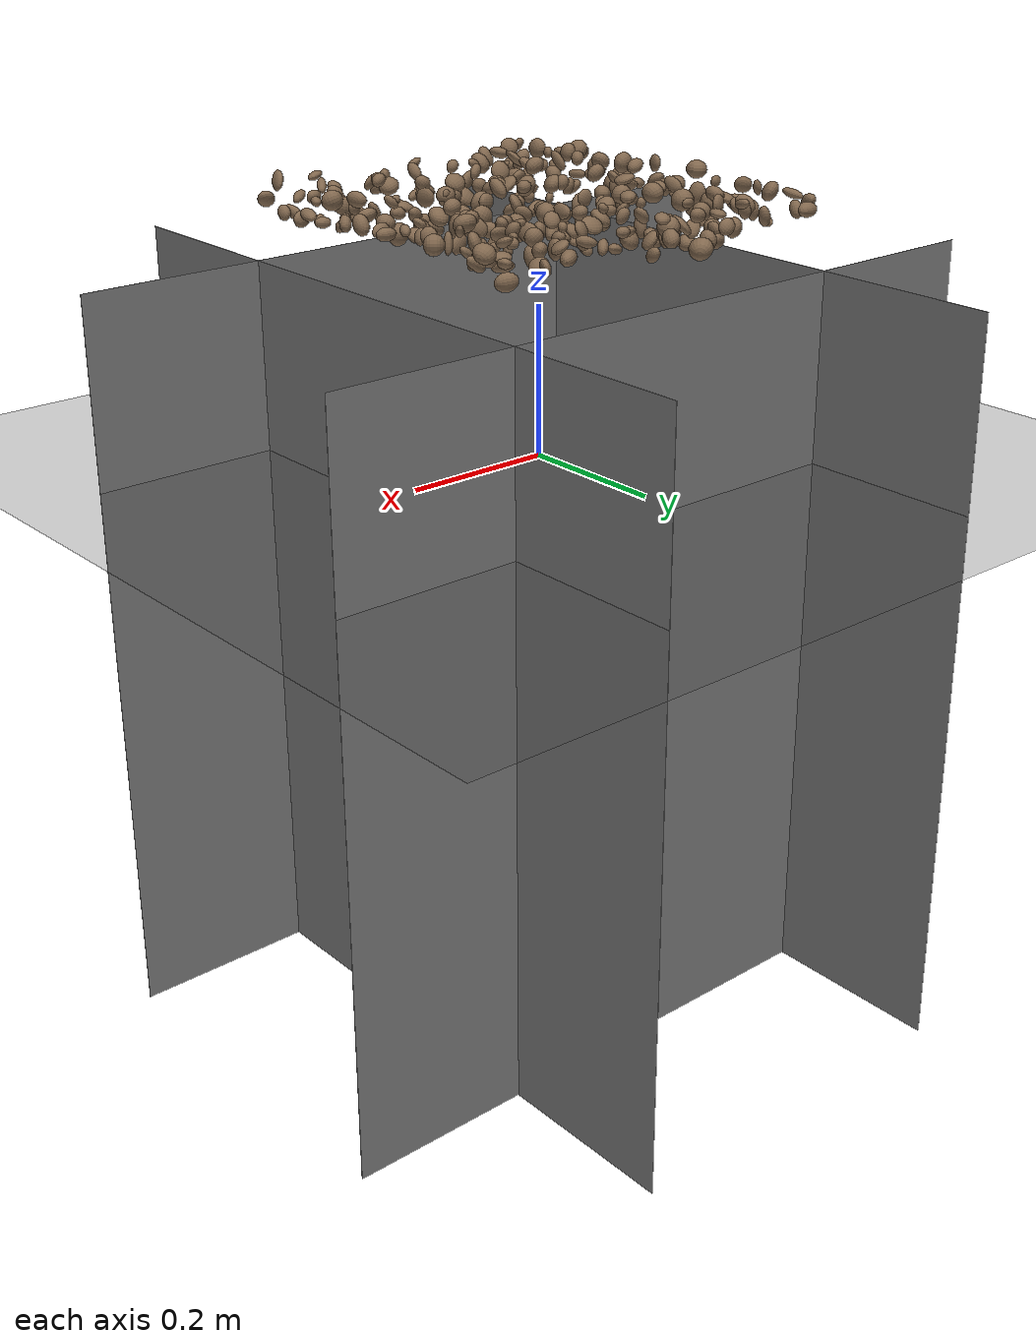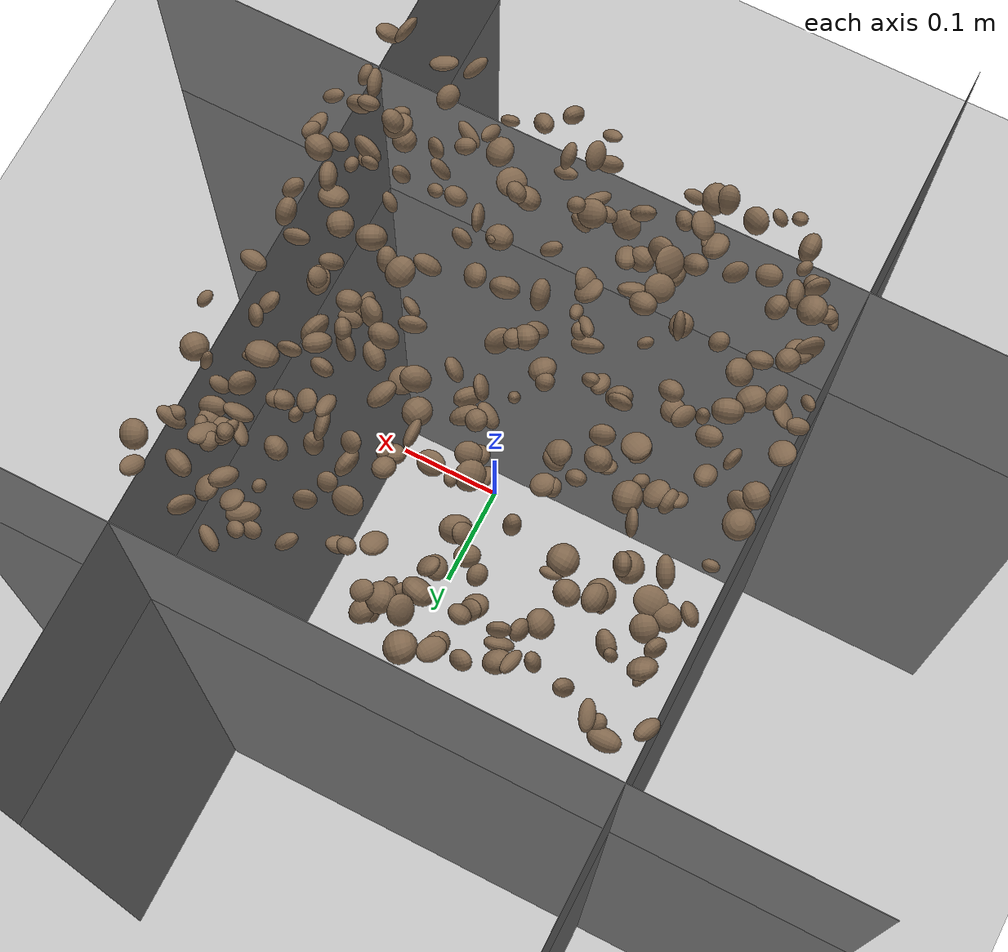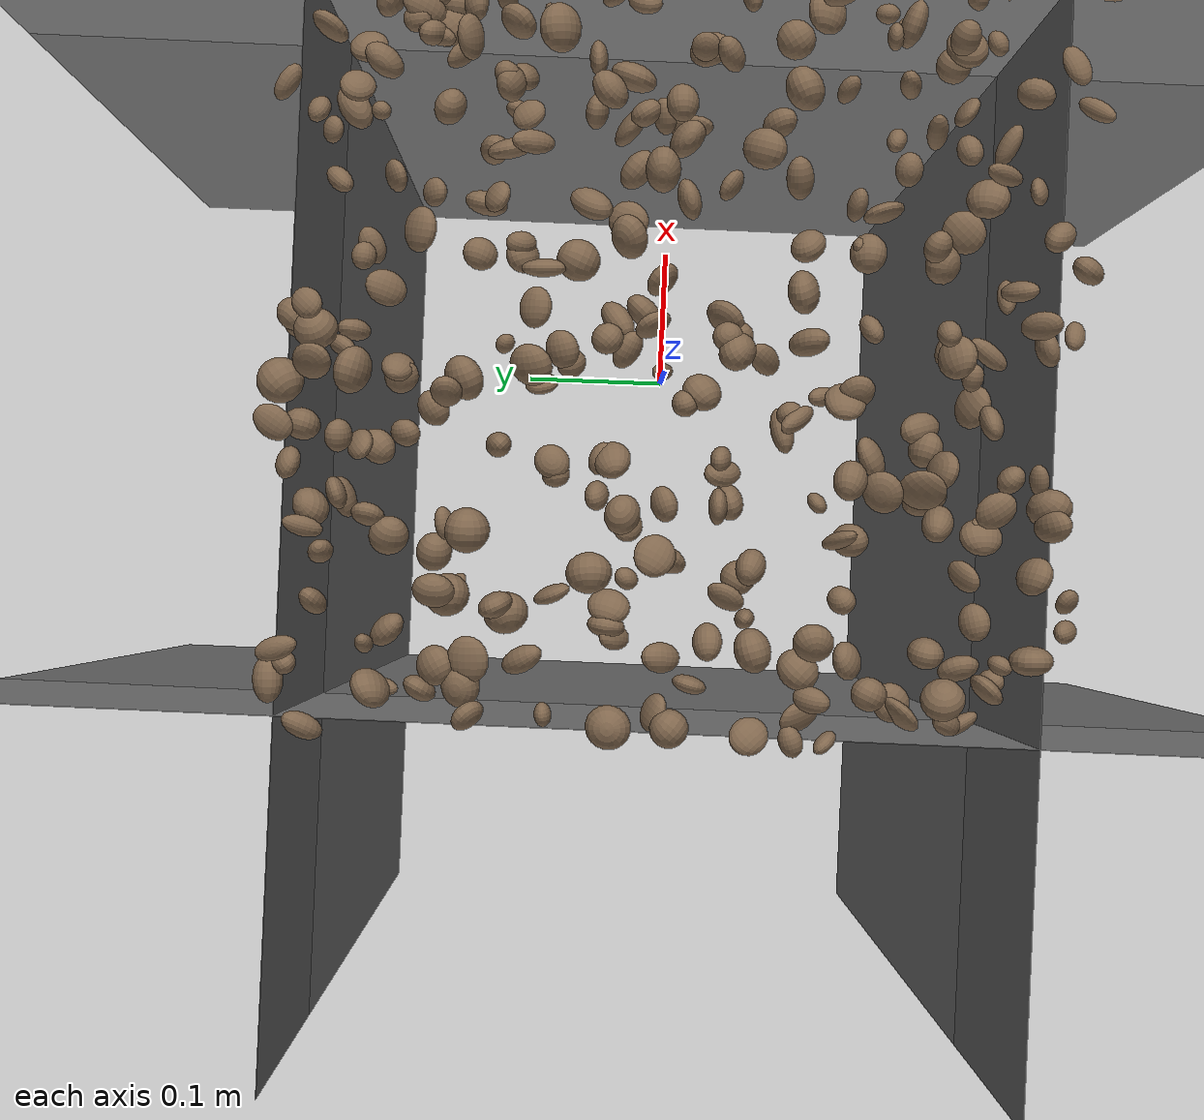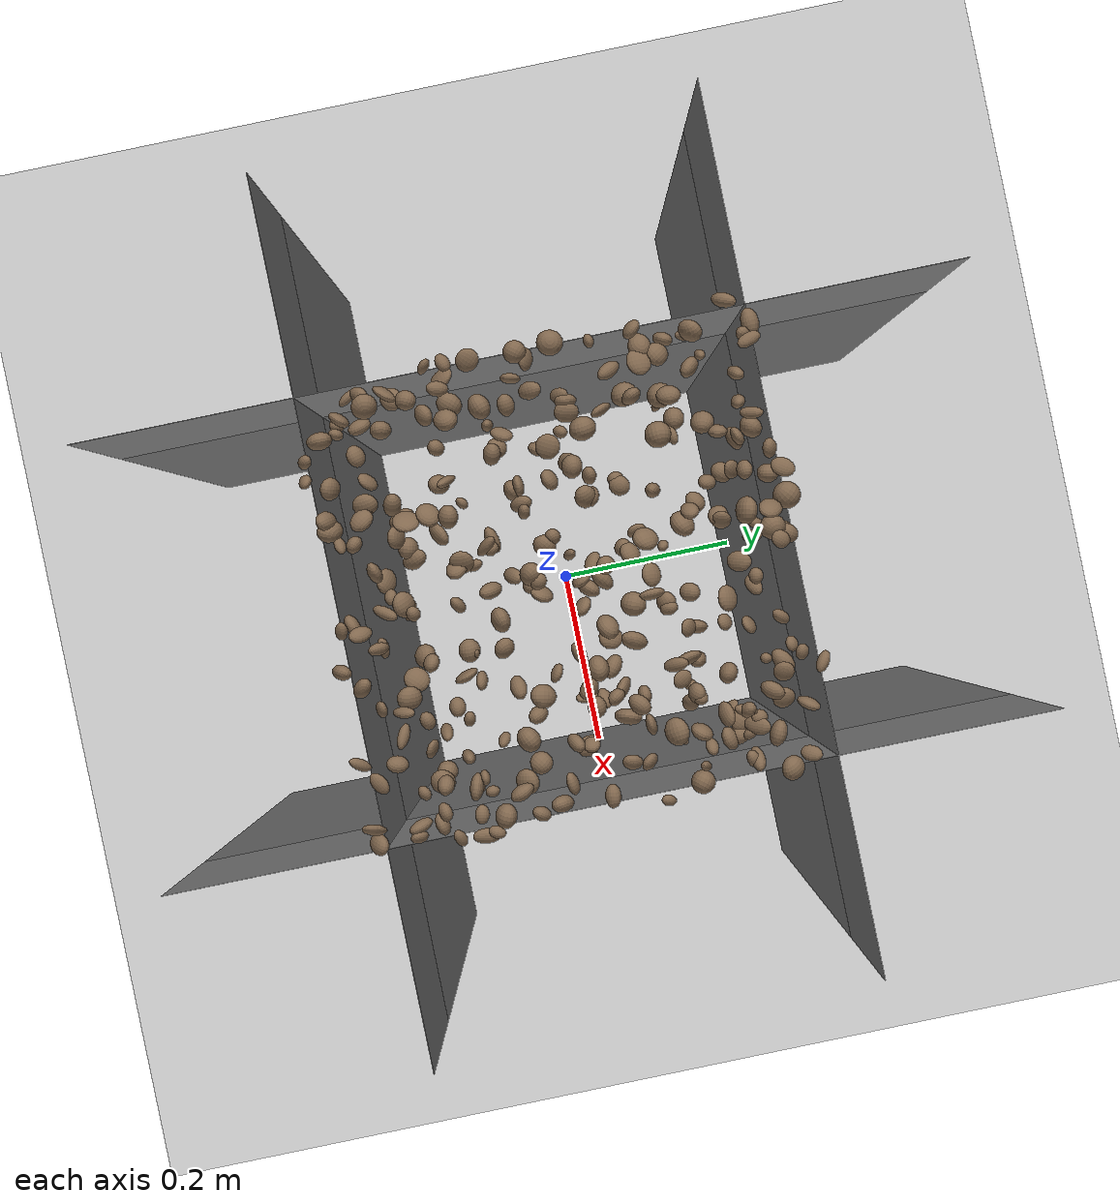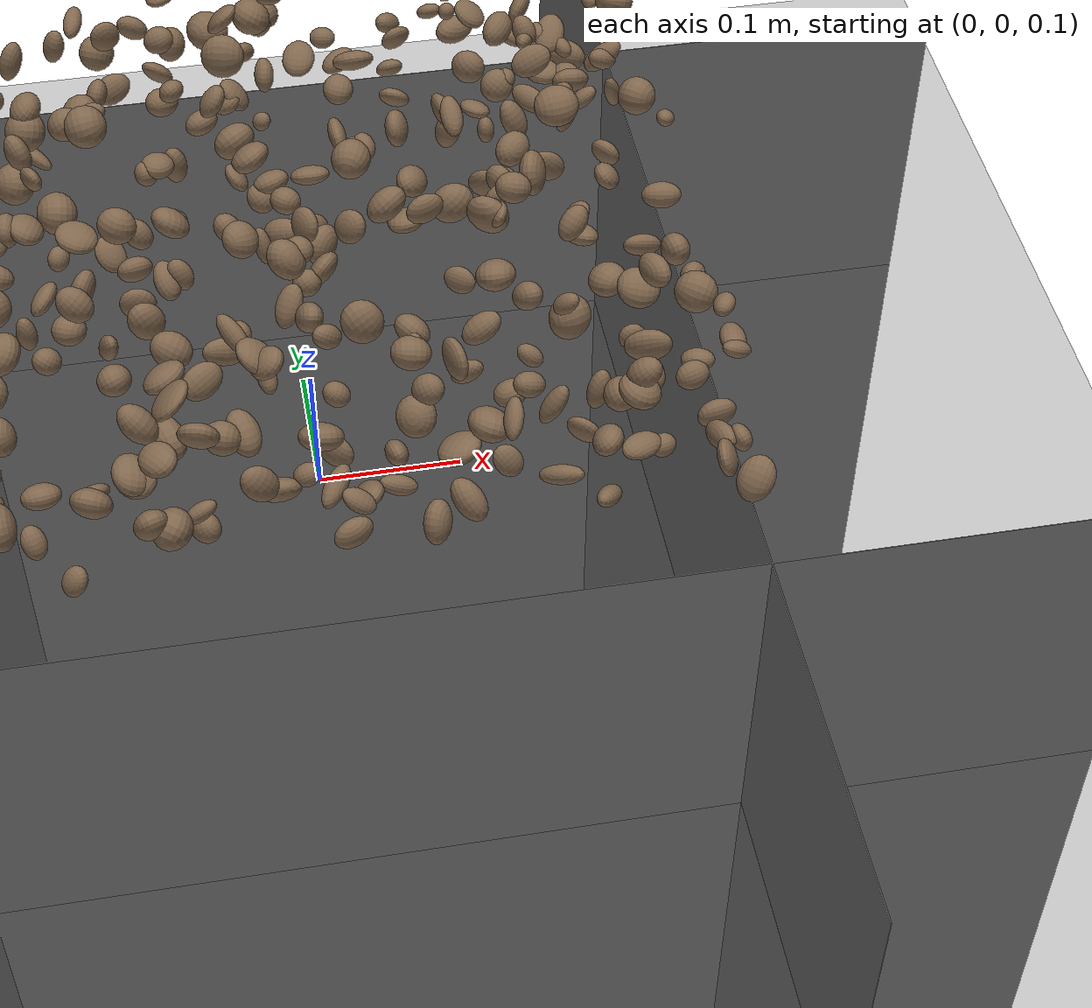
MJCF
<mujoco model="rocky_terrain_scene">

  <default>
    <default class="wall">
      <geom type="plane" size=".5 .5 .05" />
    </default>
  </default>

    <compiler angle="radian" inertiafromgeom="true" />
    <option timestep="0.002" gravity="0 0 -9.81" />

    <worldbody>

        <geom name="+x" class="wall" zaxis="1 0 0" pos="-.25 0 -.25" />
        <geom name="-x" class="wall" zaxis="-1 0 0" pos=".25 0 -.25" />
        <geom name="+y" class="wall" zaxis="0 1 0" pos="0 -.25 -.25" />
        <geom name="-y" class="wall" zaxis="0 -1 0" pos="0 .25 -.25" />

        <light name="sunlight" pos="5 5 5" dir="-1 -1 -1" diffuse="1 1 1" specular="0.5 0.5 0.5" ambient="0.5 0.5 0.5" />

        <geom name="ground_plane" type="plane" size="50 50 0.1" rgba="0.3 0.3 0.3 1" />

        <body name="rocky_terrain_body">

        </body>
    <body name="rock1" pos="0.17306365620272102 0.1545367621749637 0.34431471981199274"><joint type="free" /><geom type="ellipsoid" size="0.012760426425857913 0.006696232443501394 0.005900240014453047" quat="0.27349163613321126 0.32887277670437265 0.2806448475282253 0.11699073963419067" rgba="0.5 0.4 0.3 1" /><inertial pos="0.17306365620272102 0.1545367621749637 0.34431471981199274" quat="0.27349163613321126 0.32887277670437265 0.2806448475282253 0.11699073963419067" mass="3.4918521659649905e-05" /></body><body name="rock2" pos="0.05059145260570147 -0.24924045211702878 0.3267547923940236"><joint type="free" /><geom type="ellipsoid" size="0.009625671289405495 0.013372239969691804 0.007720580070940295" quat="0.4175831708849428 0.25173647788695663 0.23986538409592384 0.0908149671321768" rgba="0.5 0.4 0.3 1" /><inertial pos="0.05059145260570147 -0.24924045211702878 0.3267547923940236" quat="0.4175831708849428 0.25173647788695663 0.23986538409592384 0.0908149671321768" mass="1.7119331724158447e-05" /></body><body name="rock3" pos="-0.06550441848658456 0.2428596509119189 0.3466212016244134"><joint type="free" /><geom type="ellipsoid" size="0.01017216737768712 0.005421978894117081 0.013045101525675354" quat="0.1565551591396709 0.07414455841729553 0.38934086667355045 0.37995941576948306" rgba="0.5 0.4 0.3 1" /><inertial pos="-0.06550441848658456 0.2428596509119189 0.3466212016244134" quat="0.1565551591396709 0.07414455841729553 0.38934086667355045 0.37995941576948306" mass="7.665132955901988e-05" /></body><body name="rock4" pos="-0.235384271192412 0.07290943950218354 0.3341629487622615"><joint type="free" /><geom type="ellipsoid" size="0.005353862039386267 0.007500468650878365 0.007593486466691284" quat="0.2708730820357598 0.20072704363214758 0.24127100559494294 0.2871288687371496" rgba="0.5 0.4 0.3 1" /><inertial pos="-0.235384271192412 0.07290943950218354 0.3341629487622615" quat="0.2708730820357598 0.20072704363214758 0.24127100559494294 0.2871288687371496" mass="9.45135761363059e-05" /></body><body name="rock5" pos="-0.16264819850016482 0.13462853549362735 0.30624989714083545"><joint type="free" /><geom type="ellipsoid" size="0.01448550229421305 0.0073570193109387776 0.00503938395070213" quat="0.1312234724768888 0.17794768318723847 0.16877061524933398 0.5220582290865388" rgba="0.5 0.4 0.3 1" /><inertial pos="-0.16264819850016482 0.13462853549362735 0.30624989714083545" quat="0.1312234724768888 0.17794768318723847 0.16877061524933398 0.5220582290865388" mass="7.635670039494465e-05" /></body><body name="rock6" pos="-0.17188841351692263 -0.048501087282057875 0.3183586877149185"><joint type="free" /><geom type="ellipsoid" size="0.006460841645259263 0.01252516608333441 0.005921637353938795" quat="0.12332779357902394 0.1051140894607394 0.3876218421465348 0.3839362748137019" rgba="0.5 0.4 0.3 1" /><inertial pos="-0.17188841351692263 -0.048501087282057875 0.3183586877149185" quat="0.12332779357902394 0.1051140894607394 0.3876218421465348 0.3839362748137019" mass="3.7191182338132084e-05" /></body><body name="rock7" pos="0.23166430866940968 -0.05125702094839446 0.32677797743045733"><joint type="free" /><geom type="ellipsoid" size="0.010481162023701484 0.013837003979753966 0.00893656464028618" quat="0.14928000696628813 0.2882764916150756 0.1751507225715991 0.38729277884703717" rgba="0.5 0.4 0.3 1" /><inertial pos="0.23166430866940968 -0.05125702094839446 0.32677797743045733" quat="0.14928000696628813 0.2882764916150756 0.1751507225715991 0.38729277884703717" mass="9.443539200709004e-05" /></body><body name="rock8" pos="-0.16171329600179474 0.0705099340880645 0.33985104950010375"><joint type="free" /><geom type="ellipsoid" size="0.01304992605326286 0.008489180610981088 0.005061007134241644" quat="0.31233378568901066 0.07754390536357368 0.3357520399917156 0.27437026895570005" rgba="0.5 0.4 0.3 1" /><inertial pos="-0.16171329600179474 0.0705099340880645 0.33985104950010375" quat="0.31233378568901066 0.07754390536357368 0.3357520399917156 0.27437026895570005" mass="6.316793800334985e-05" /></body><body name="rock9" pos="-0.17502374788284458 0.09871633510593636 0.31408511703694775"><joint type="free" /><geom type="ellipsoid" size="0.01384025246878072 0.014138207645357025 0.012566864211275577" quat="0.04262648626882291 0.4356459956284565 0.22150063806350986 0.3002268800392108" rgba="0.5 0.4 0.3 1" /><inertial pos="-0.17502374788284458 0.09871633510593636 0.31408511703694775" quat="0.04262648626882291 0.4356459956284565 0.22150063806350986 0.3002268800392108" mass="2.9765232585218687e-05" /></body><body name="rock10" pos="0.2048894984669345 -0.12077460211560109 0.31812106367663207"><joint type="free" /><geom type="ellipsoid" size="0.007452927285758465 0.0061442587160838846 0.006679356424680487" quat="0.06590445631800403 0.4455953948182821 0.44456969972865423 0.0439304491350597" rgba="0.5 0.4 0.3 1" /><inertial pos="0.2048894984669345 -0.12077460211560109 0.31812106367663207" quat="0.06590445631800403 0.4455953948182821 0.44456969972865423 0.0439304491350597" mass="7.075252838802611e-05" /></body><body name="rock11" pos="-0.09350139989644557 -0.15538416000705935 0.32358452263829013"><joint type="free" /><geom type="ellipsoid" size="0.014717138581658285 0.011108745739058516 0.010086348412098468" quat="0.16385698796546286 0.2475519326827148 0.26454404261479114 0.3240470367370311" rgba="0.5 0.4 0.3 1" /><inertial pos="-0.09350139989644557 -0.15538416000705935 0.32358452263829013" quat="0.16385698796546286 0.2475519326827148 0.26454404261479114 0.3240470367370311" mass="7.388667747819396e-05" /></body><body name="rock12" pos="0.1712132242219953 0.19848216294267812 0.31557940897572384"><joint type="free" /><geom type="ellipsoid" size="0.012139436304966111 0.012113928474370567 0.006607322299979938" quat="0.38667670153656686 0.09105045757828813 0.14927252276319322 0.3730003181219518" rgba="0.5 0.4 0.3 1" /><inertial pos="0.1712132242219953 0.19848216294267812 0.31557940897572384" quat="0.38667670153656686 0.09105045757828813 0.14927252276319322 0.3730003181219518" mass="6.365801514124291e-05" /></body><body name="rock13" pos="-0.20438428394280467 0.12031095182666834 0.32565632591152627"><joint type="free" /><geom type="ellipsoid" size="0.00614333653076464 0.013389989814509583 0.014887092457070063" quat="0.05460319813867654 0.3893997227178711 0.06388156613722415 0.49211551300622824" rgba="0.5 0.4 0.3 1" /><inertial pos="-0.20438428394280467 0.12031095182666834 0.32565632591152627" quat="0.05460319813867654 0.3893997227178711 0.06388156613722415 0.49211551300622824" mass="6.674973491199052e-05" /></body><body name="rock14" pos="-0.07693185247587936 0.04350214837762145 0.315292452842859"><joint type="free" /><geom type="ellipsoid" size="0.010682246392691013 0.008112201107316688 0.007781062701480119" quat="0.11711101246995531 0.037140824452859614 0.3016397013740942 0.5441084617030909" rgba="0.5 0.4 0.3 1" /><inertial pos="-0.07693185247587936 0.04350214837762145 0.315292452842859" quat="0.11711101246995531 0.037140824452859614 0.3016397013740942 0.5441084617030909" mass="2.430052690778933e-05" /></body><body name="rock15" pos="-0.1144387298369477 0.22166787800900556 0.319132147570852"><joint type="free" /><geom type="ellipsoid" size="0.01047134399549099 0.01284432962157591 0.012105098711496528" quat="0.2596275462770118 0.0028729228229082203 0.21140611801192363 0.5260934128881565" rgba="0.5 0.4 0.3 1" /><inertial pos="-0.1144387298369477 0.22166787800900556 0.319132147570852" quat="0.2596275462770118 0.0028729228229082203 0.21140611801192363 0.5260934128881565" mass="2.9346125629122468e-05" /></body><body name="rock16" pos="0.08048104222400632 0.05693464661089209 0.3137295610039314"><joint type="free" /><geom type="ellipsoid" size="0.010626711722269457 0.014944468414155705 0.00843948394579671" quat="0.19389150994373613 0.26707037809380685 0.04542788163766225 0.49361023032479473" rgba="0.5 0.4 0.3 1" /><inertial pos="0.08048104222400632 0.05693464661089209 0.3137295610039314" quat="0.19389150994373613 0.26707037809380685 0.04542788163766225 0.49361023032479473" mass="1.7030064640318202e-05" /></body><body name="rock17" pos="-0.23117207899075543 -0.0866854593650136 0.3040612766059689"><joint type="free" /><geom type="ellipsoid" size="0.005312223085993266 0.014568574185873158 0.011141577220656836" quat="0.5268121244615294 0.0284964828435341 0.2723559687789588 0.17233542391597775" rgba="0.5 0.4 0.3 1" /><inertial pos="-0.23117207899075543 -0.0866854593650136 0.3040612766059689" quat="0.5268121244615294 0.0284964828435341 0.2723559687789588 0.17233542391597775" mass="3.494006974978212e-05" /></body><body name="rock18" pos="0.10960126055156866 0.10781219444756723 0.3276433618707833"><joint type="free" /><geom type="ellipsoid" size="0.014608279776293299 0.011686625835475794 0.006147375242630744" quat="0.2745831214019419 0.16999919758960916 0.26013563094303105 0.2952820500654179" rgba="0.5 0.4 0.3 1" /><inertial pos="0.10960126055156866 0.10781219444756723 0.3276433618707833" quat="0.2745831214019419 0.16999919758960916 0.26013563094303105 0.2952820500654179" mass="4.13951044113721e-05" /></body><body name="rock19" pos="0.01636285646272384 0.021173915808726407 0.30020946392174896"><joint type="free" /><geom type="ellipsoid" size="0.01364211775714708 0.011568301684374255 0.008355601616614725" quat="0.31108347878780174 0.38315641192900973 0.046863701750637254 0.25889640753255133" rgba="0.5 0.4 0.3 1" /><inertial pos="0.01636285646272384 0.021173915808726407 0.30020946392174896" quat="0.31108347878780174 0.38315641192900973 0.046863701750637254 0.25889640753255133" mass="2.6851869102875344e-05" /></body><body name="rock20" pos="-0.10341663286397018 -0.02945271485996015 0.31472559151650015"><joint type="free" /><geom type="ellipsoid" size="0.00588134717699919 0.011317290195346445 0.0115685303682574" quat="0.12409827180334095 0.37447121494806573 0.37496403794781763 0.1264664753007756" rgba="0.5 0.4 0.3 1" /><inertial pos="-0.10341663286397018 -0.02945271485996015 0.31472559151650015" quat="0.12409827180334095 0.37447121494806573 0.37496403794781763 0.1264664753007756" mass="5.2727357135197234e-05" /></body><body name="rock21" pos="-0.140089584189188 -0.04949545020679713 0.3385957976644303"><joint type="free" /><geom type="ellipsoid" size="0.009065783801271272 0.010327704487776836 0.012541998756076358" quat="0.19648767765244204 0.3605670425774437 0.3646259273894187 0.07831935238069558" rgba="0.5 0.4 0.3 1" /><inertial pos="-0.140089584189188 -0.04949545020679713 0.3385957976644303" quat="0.19648767765244204 0.3605670425774437 0.3646259273894187 0.07831935238069558" mass="5.6743854502805186e-05" /></body><body name="rock22" pos="-0.1136739894136698 -0.19115426321926282 0.33067144345821264"><joint type="free" /><geom type="ellipsoid" size="0.01153855080281084 0.006665684170349446 0.01210132575113471" quat="0.2466625856410568 0.4305727932110605 0.12218015449079753 0.20058446665708518" rgba="0.5 0.4 0.3 1" /><inertial pos="-0.1136739894136698 -0.19115426321926282 0.33067144345821264" quat="0.2466625856410568 0.4305727932110605 0.12218015449079753 0.20058446665708518" mass="1.7399990854472243e-05" /></body><body name="rock23" pos="-0.11564656494305936 -0.18944383148120508 0.33273929991750595"><joint type="free" /><geom type="ellipsoid" size="0.013678767954106968 0.008363288776267977 0.012077126695608072" quat="0.14620932323535263 0.33154840547031583 0.2987401320611374 0.22350213923319406" rgba="0.5 0.4 0.3 1" /><inertial pos="-0.11564656494305936 -0.18944383148120508 0.33273929991750595" quat="0.14620932323535263 0.33154840547031583 0.2987401320611374 0.22350213923319406" mass="5.691426884532765e-05" /></body><body name="rock24" pos="-0.03648618100267931 -0.10351956281150149 0.32945163054205284"><joint type="free" /><geom type="ellipsoid" size="0.013008699221861621 0.006778485681079951 0.014072055248020878" quat="0.16123011426709388 0.35531225369197594 0.3198529562583477 0.16360467578258248" rgba="0.5 0.4 0.3 1" /><inertial pos="-0.03648618100267931 -0.10351956281150149 0.32945163054205284" quat="0.16123011426709388 0.35531225369197594 0.3198529562583477 0.16360467578258248" mass="1.3753178854456812e-05" /></body><body name="rock25" pos="-0.04105928167279871 0.14043886613819206 0.33056236161922326"><joint type="free" /><geom type="ellipsoid" size="0.009774762697988802 0.012168499604789797 0.006459201883205804" quat="0.1725149220425352 0.31187794616310804 0.3530900159231143 0.1625171158712425" rgba="0.5 0.4 0.3 1" /><inertial pos="-0.04105928167279871 0.14043886613819206 0.33056236161922326" quat="0.1725149220425352 0.31187794616310804 0.3530900159231143 0.1625171158712425" mass="6.877456642816026e-05" /></body><body name="rock26" pos="-0.08920692430362498 0.07125707227098843 0.33323068120723687"><joint type="free" /><geom type="ellipsoid" size="0.008785049480359209 0.008307973816775846 0.007425616750176227" quat="0.31615081123454714 0.13910848406364396 0.32969530403763225 0.21504540066417674" rgba="0.5 0.4 0.3 1" /><inertial pos="-0.08920692430362498 0.07125707227098843 0.33323068120723687" quat="0.31615081123454714 0.13910848406364396 0.32969530403763225 0.21504540066417674" mass="7.532248626847265e-05" /></body><body name="rock27" pos="0.23759426772725595 -0.07461139715397186 0.3250587653286591"><joint type="free" /><geom type="ellipsoid" size="0.011409786756359477 0.008756411021738351 0.007425814376742898" quat="0.3799847602806413 0.28505084111071616 0.30716526529071364 0.027799133317928874" rgba="0.5 0.4 0.3 1" /><inertial pos="0.23759426772725595 -0.07461139715397186 0.3250587653286591" quat="0.3799847602806413 0.28505084111071616 0.30716526529071364 0.027799133317928874" mass="9.815742065160363e-05" /></body><body name="rock28" pos="-0.07480845842580452 0.19299920836213608 0.3189471240833129"><joint type="free" /><geom type="ellipsoid" size="0.005611990937419971 0.012782228943723824 0.009309859942227328" quat="0.3268453828420396 0.35093847625824526 0.03273485146541613 0.28948128943429896" rgba="0.5 0.4 0.3 1" /><inertial pos="-0.07480845842580452 0.19299920836213608 0.3189471240833129" quat="0.3268453828420396 0.35093847625824526 0.03273485146541613 0.28948128943429896" mass="9.439118313689372e-05" /></body><body name="rock29" pos="0.05969846776831256 -0.11069695872540847 0.32516463676147367"><joint type="free" /><geom type="ellipsoid" size="0.005710460396059655 0.011582633684079208 0.006026905798736751" quat="0.34025061253575956 0.1873865100375901 0.2607852973070666 0.21157758011958366" rgba="0.5 0.4 0.3 1" /><inertial pos="0.05969846776831256 -0.11069695872540847 0.32516463676147367" quat="0.34025061253575956 0.1873865100375901 0.2607852973070666 0.21157758011958366" mass="1.5659509412950587e-05" /></body><body name="rock30" pos="-0.13911617247027935 0.14417538340477354 0.3220228157369113"><joint type="free" /><geom type="ellipsoid" size="0.011020595614977336 0.011008723338690542 0.012378150363801747" quat="0.36959728208806775 0.18021761488814428 0.15473734271231399 0.29544776031147385" rgba="0.5 0.4 0.3 1" /><inertial pos="-0.13911617247027935 0.14417538340477354 0.3220228157369113" quat="0.36959728208806775 0.18021761488814428 0.15473734271231399 0.29544776031147385" mass="7.25058686294022e-05" /></body><body name="rock31" pos="0.20712224807413382 0.04681856165179349 0.3279733589476309"><joint type="free" /><geom type="ellipsoid" size="0.006050631371555393 0.010421389706277638 0.010099655515964276" quat="0.2858956856579338 0.41866609587050235 0.10294824488348019 0.19248997358808378" rgba="0.5 0.4 0.3 1" /><inertial pos="0.20712224807413382 0.04681856165179349 0.3279733589476309" quat="0.2858956856579338 0.41866609587050235 0.10294824488348019 0.19248997358808378" mass="3.0836446399082034e-05" /></body><body name="rock32" pos="-0.0023077654541815984 0.20177430192276774 0.3004422588589903"><joint type="free" /><geom type="ellipsoid" size="0.011805904202321998 0.008339912136090921 0.006686664290919409" quat="0.15191063408942881 0.3682196428479423 0.1408017718875123 0.3390679511751165" rgba="0.5 0.4 0.3 1" /><inertial pos="-0.0023077654541815984 0.20177430192276774 0.3004422588589903" quat="0.15191063408942881 0.3682196428479423 0.1408017718875123 0.3390679511751165" mass="2.3203928640486606e-05" /></body><body name="rock33" pos="0.0018115392833218946 -0.16739928482953248 0.30765696058690484"><joint type="free" /><geom type="ellipsoid" size="0.005802120518154593 0.012233616610183946 0.009747572091970913" quat="0.4605138642612213 0.1194481913167166 0.13765518371031432 0.2823827607117479" rgba="0.5 0.4 0.3 1" /><inertial pos="0.0018115392833218946 -0.16739928482953248 0.30765696058690484" quat="0.4605138642612213 0.1194481913167166 0.13765518371031432 0.2823827607117479" mass="3.833811195235294e-05" /></body><body name="rock34" pos="0.18660530914582524 -0.1658460346470429 0.3384844405480816"><joint type="free" /><geom type="ellipsoid" size="0.009060121420471582 0.008951663152168911 0.011874825813586457" quat="0.2854466414472516 0.20384483008832774 0.06451097106728111 0.44619755739713957" rgba="0.5 0.4 0.3 1" /><inertial pos="0.18660530914582524 -0.1658460346470429 0.3384844405480816" quat="0.2854466414472516 0.20384483008832774 0.06451097106728111 0.44619755739713957" mass="7.206279595313287e-05" /></body><body name="rock35" pos="0.0875303454007757 0.17587746529035753 0.33966203458316824"><joint type="free" /><geom type="ellipsoid" size="0.005346027784838744 0.010770832721038102 0.010058220547498099" quat="0.14894070260768896 0.25972670344555576 0.23502066579545494 0.35631192815130036" rgba="0.5 0.4 0.3 1" /><inertial pos="0.0875303454007757 0.17587746529035753 0.33966203458316824" quat="0.14894070260768896 0.25972670344555576 0.23502066579545494 0.35631192815130036" mass="9.339772787207822e-05" /></body><body name="rock36" pos="-0.22033659189724314 -0.09207537718811543 0.31848814607805265"><joint type="free" /><geom type="ellipsoid" size="0.007701505071126143 0.0121259632836756 0.008256991096412645" quat="0.12427594147861855 0.3513223390198853 0.05229559167718052 0.47210612782431555" rgba="0.5 0.4 0.3 1" /><inertial pos="-0.22033659189724314 -0.09207537718811543 0.31848814607805265" quat="0.12427594147861855 0.3513223390198853 0.05229559167718052 0.47210612782431555" mass="5.6029104283871674e-05" /></body><body name="rock37" pos="-0.20215974066077785 -0.08341531363448923 0.3133206336309893"><joint type="free" /><geom type="ellipsoid" size="0.012809061050585109 0.010812728930331347 0.013816085439895584" quat="0.02289936127097272 0.26310214111936653 0.33157405577383264 0.3824244418358281" rgba="0.5 0.4 0.3 1" /><inertial pos="-0.20215974066077785 -0.08341531363448923 0.3133206336309893" quat="0.02289936127097272 0.26310214111936653 0.33157405577383264 0.3824244418358281" mass="5.731508287621052e-05" /></body><body name="rock38" pos="0.041896141410760535 0.1226201149825068 0.3433361940960476"><joint type="free" /><geom type="ellipsoid" size="0.008313633697603883 0.01083441687926997 0.009800153789332886" quat="0.390990263427151 0.1344070154809439 0.4732823423184935 0.001320378773411601" rgba="0.5 0.4 0.3 1" /><inertial pos="0.041896141410760535 0.1226201149825068 0.3433361940960476" quat="0.390990263427151 0.1344070154809439 0.4732823423184935 0.001320378773411601" mass="5.2745819718779444e-05" /></body><body name="rock39" pos="-0.1725552320923892 0.21722161342584628 0.32316439829688737"><joint type="free" /><geom type="ellipsoid" size="0.008395506927509776 0.014152791272764028 0.007122018200440972" quat="0.31996549829513865 0.3178334629038843 0.2528678199022646 0.10933321889871242" rgba="0.5 0.4 0.3 1" /><inertial pos="-0.1725552320923892 0.21722161342584628 0.32316439829688737" quat="0.31996549829513865 0.3178334629038843 0.2528678199022646 0.10933321889871242" mass="1.0181648435013281e-05" /></body><body name="rock40" pos="0.18765671082702912 0.10638361895111081 0.3278787855896851"><joint type="free" /><geom type="ellipsoid" size="0.012287053570836915 0.012404871656159597 0.007784322346422312" quat="0.277316773075153 0.393620673031472 0.19305925281125788 0.13600330108211708" rgba="0.5 0.4 0.3 1" /><inertial pos="0.18765671082702912 0.10638361895111081 0.3278787855896851" quat="0.277316773075153 0.393620673031472 0.19305925281125788 0.13600330108211708" mass="4.921305125528545e-05" /></body><body name="rock41" pos="-0.006896750888952474 0.2210190515719393 0.33626818845285955"><joint type="free" /><geom type="ellipsoid" size="0.013395500591255095 0.013979212484012231 0.011813368767427543" quat="0.09284797674863432 0.17618230761118023 0.1203724320407822 0.6105972835994031" rgba="0.5 0.4 0.3 1" /><inertial pos="-0.006896750888952474 0.2210190515719393 0.33626818845285955" quat="0.09284797674863432 0.17618230761118023 0.1203724320407822 0.6105972835994031" mass="5.5181248435159684e-05" /></body><body name="rock42" pos="-0.08356849960000279 -0.03024725461112543 0.3317480003251274"><joint type="free" /><geom type="ellipsoid" size="0.008698245183573663 0.01292073239509487 0.007152510951101344" quat="0.5641854955736253 0.16475609855871132 0.164654065678621 0.10640434018904232" rgba="0.5 0.4 0.3 1" /><inertial pos="-0.08356849960000279 -0.03024725461112543 0.3317480003251274" quat="0.5641854955736253 0.16475609855871132 0.164654065678621 0.10640434018904232" mass="5.3688300118570605e-05" /></body><body name="rock43" pos="-0.24190243715491078 -0.005044345229166469 0.31748359538429016"><joint type="free" /><geom type="ellipsoid" size="0.012321694804383191 0.01154859133553083 0.012075595117059305" quat="0.1043333465441794 0.15375357483590235 0.33444522798579934 0.40746785063411894" rgba="0.5 0.4 0.3 1" /><inertial pos="-0.24190243715491078 -0.005044345229166469 0.31748359538429016" quat="0.1043333465441794 0.15375357483590235 0.33444522798579934 0.40746785063411894" mass="4.973192599214921e-05" /></body><body name="rock44" pos="0.17022986735313778 -0.23186358637944476 0.34863935146727104"><joint type="free" /><geom type="ellipsoid" size="0.01308680680817919 0.005140537247788105 0.008176533689402604" quat="0.3532065736504752 0.4591851453820888 0.13132494364523736 0.056283337322198625" rgba="0.5 0.4 0.3 1" /><inertial pos="0.17022986735313778 -0.23186358637944476 0.34863935146727104" quat="0.3532065736504752 0.4591851453820888 0.13132494364523736 0.056283337322198625" mass="9.886699076371549e-05" /></body><body name="rock45" pos="-0.2378502544994915 0.1186705553239325 0.33686651394872635"><joint type="free" /><geom type="ellipsoid" size="0.011273587822305604 0.010922344321107324 0.00674322460767051" quat="0.060743913332168525 0.26377753662050535 0.3648206567369264 0.31065789331039967" rgba="0.5 0.4 0.3 1" /><inertial pos="-0.2378502544994915 0.1186705553239325 0.33686651394872635" quat="0.060743913332168525 0.26377753662050535 0.3648206567369264 0.31065789331039967" mass="5.335988872377744e-05" /></body><body name="rock46" pos="-0.10704720693676545 0.20367123096922846 0.30070329905393095"><joint type="free" /><geom type="ellipsoid" size="0.006614281126893782 0.010001148439747948 0.013391800877366595" quat="0.3094296099570009 0.11578219564499051 0.2816865258539838 0.29310166854402486" rgba="0.5 0.4 0.3 1" /><inertial pos="-0.10704720693676545 0.20367123096922846 0.30070329905393095" quat="0.3094296099570009 0.11578219564499051 0.2816865258539838 0.29310166854402486" mass="4.8589089505033713e-05" /></body><body name="rock47" pos="0.11384862245496058 0.11901335971822391 0.301303919759888"><joint type="free" /><geom type="ellipsoid" size="0.008977874442954465 0.013968046115611556 0.00848721395791193" quat="0.2565934371971711 0.3259203977668329 0.21016083126152438 0.2073253337744716" rgba="0.5 0.4 0.3 1" /><inertial pos="0.11384862245496058 0.11901335971822391 0.301303919759888" quat="0.2565934371971711 0.3259203977668329 0.21016083126152438 0.2073253337744716" mass="9.469395101554855e-05" /></body><body name="rock48" pos="0.004450897938384213 -0.23083776271232703 0.3057874369610475"><joint type="free" /><geom type="ellipsoid" size="0.007214211303908505 0.012350937737789372 0.009585586136202851" quat="0.019822602899589082 0.37011338405953126 0.5451033810114108 0.0649606320294689" rgba="0.5 0.4 0.3 1" /><inertial pos="0.004450897938384213 -0.23083776271232703 0.3057874369610475" quat="0.019822602899589082 0.37011338405953126 0.5451033810114108 0.0649606320294689" mass="7.423480932243513e-05" /></body><body name="rock49" pos="-0.190458579791684 -0.05230173609148425 0.3451287171363372"><joint type="free" /><geom type="ellipsoid" size="0.011132734220395998 0.013457244397222706 0.013852267044178999" quat="0.24644444974117333 0.1694807784268297 0.3137813491437866 0.2702934226882104" rgba="0.5 0.4 0.3 1" /><inertial pos="-0.190458579791684 -0.05230173609148425 0.3451287171363372" quat="0.24644444974117333 0.1694807784268297 0.3137813491437866 0.2702934226882104" mass="5.4560219858902554e-05" /></body><body name="rock50" pos="-0.035984018669798556 -0.014875354181559108 0.3444178492512097"><joint type="free" /><geom type="ellipsoid" size="0.009706232066010493 0.0121272813964041 0.012258019258770299" quat="0.2631284912470416 0.006423159953433587 0.5042940874388843 0.2261542613606405" rgba="0.5 0.4 0.3 1" /><inertial pos="-0.035984018669798556 -0.014875354181559108 0.3444178492512097" quat="0.2631284912470416 0.006423159953433587 0.5042940874388843 0.2261542613606405" mass="4.495670104078426e-05" /></body><body name="rock51" pos="0.04221678329207157 0.06323684488713699 0.33284459129984506"><joint type="free" /><geom type="ellipsoid" size="0.012732868657601131 0.01256257185195805 0.01344752493130123" quat="0.12452291386837942 0.043708275759319695 0.3871855244578768 0.444583285914424" rgba="0.5 0.4 0.3 1" /><inertial pos="0.04221678329207157 0.06323684488713699 0.33284459129984506" quat="0.12452291386837942 0.043708275759319695 0.3871855244578768 0.444583285914424" mass="2.9738398888755846e-05" /></body><body name="rock52" pos="0.18165347623881667 0.22234927549221867 0.3196943335575915"><joint type="free" /><geom type="ellipsoid" size="0.013072081573970336 0.010005565558027743 0.0058643000422379035" quat="0.23401951054160264 0.41300074189451774 0.13722797514965412 0.21575177241422544" rgba="0.5 0.4 0.3 1" /><inertial pos="0.18165347623881667 0.22234927549221867 0.3196943335575915" quat="0.23401951054160264 0.41300074189451774 0.13722797514965412 0.21575177241422544" mass="4.4317424144170045e-05" /></body><body name="rock53" pos="0.048800679343779185 0.1914468920540599 0.31365796669987617"><joint type="free" /><geom type="ellipsoid" size="0.012097849372799924 0.006174363359008255 0.007902856918350912" quat="0.3815361526474596 0.4394215881466034 0.02369363854221592 0.15534862066372102" rgba="0.5 0.4 0.3 1" /><inertial pos="0.048800679343779185 0.1914468920540599 0.31365796669987617" quat="0.3815361526474596 0.4394215881466034 0.02369363854221592 0.15534862066372102" mass="7.365124532120824e-05" /></body><body name="rock54" pos="0.1994345577929204 -0.13613368145510119 0.30615722156856"><joint type="free" /><geom type="ellipsoid" size="0.006752798147416151 0.01080481808981891 0.007356405339707338" quat="0.39814365928048584 0.150980496896564 0.28105874756227783 0.16981709626067237" rgba="0.5 0.4 0.3 1" /><inertial pos="0.1994345577929204 -0.13613368145510119 0.30615722156856" quat="0.39814365928048584 0.150980496896564 0.28105874756227783 0.16981709626067237" mass="8.189269783502418e-05" /></body><body name="rock55" pos="-0.09627861768656043 -0.2312363091918881 0.32943833849989596"><joint type="free" /><geom type="ellipsoid" size="0.011420746092403705 0.014765279813391943 0.012639627494429501" quat="0.011070385610899874 0.1904216230613134 0.2604365721045604 0.5380714192232263" rgba="0.5 0.4 0.3 1" /><inertial pos="-0.09627861768656043 -0.2312363091918881 0.32943833849989596" quat="0.011070385610899874 0.1904216230613134 0.2604365721045604 0.5380714192232263" mass="6.286956792747859e-05" /></body><body name="rock56" pos="0.12518983491278968 -0.12838656217141858 0.3267827966785606"><joint type="free" /><geom type="ellipsoid" size="0.006039294803876119 0.009152418206323825 0.006279336738060304" quat="0.43681952401029067 0.19082619948983223 0.07855540566487573 0.2937988708350013" rgba="0.5 0.4 0.3 1" /><inertial pos="0.12518983491278968 -0.12838656217141858 0.3267827966785606" quat="0.43681952401029067 0.19082619948983223 0.07855540566487573 0.2937988708350013" mass="1.5652211322539917e-05" /></body><body name="rock57" pos="-0.0013453219027967922 -0.029184396504262133 0.3431715868223925"><joint type="free" /><geom type="ellipsoid" size="0.009288274849052654 0.008989327633071913 0.007998809408080176" quat="0.3603098782908117 0.09272510649080451 0.021949122637292425 0.5250158925810914" rgba="0.5 0.4 0.3 1" /><inertial pos="-0.0013453219027967922 -0.029184396504262133 0.3431715868223925" quat="0.3603098782908117 0.09272510649080451 0.021949122637292425 0.5250158925810914" mass="7.168475905237236e-05" /></body><body name="rock58" pos="0.16572732567840048 -0.13912862657143177 0.30160821805150717"><joint type="free" /><geom type="ellipsoid" size="0.007163816570441885 0.013760445657249546 0.006513363978873996" quat="0.4547739718749822 0.3987196392393755 0.1334387544902813 0.013067634395361" rgba="0.5 0.4 0.3 1" /><inertial pos="0.16572732567840048 -0.13912862657143177 0.30160821805150717" quat="0.4547739718749822 0.3987196392393755 0.1334387544902813 0.013067634395361" mass="5.7959878755199966e-05" /></body><body name="rock59" pos="-0.21519784751097015 -0.16901466541455124 0.3416724133212915"><joint type="free" /><geom type="ellipsoid" size="0.013634971227176478 0.01421971836216682 0.01150886399076928" quat="0.4508503757760282 0.09162742328902534 0.18498020878941576 0.2725419921455306" rgba="0.5 0.4 0.3 1" /><inertial pos="-0.21519784751097015 -0.16901466541455124 0.3416724133212915" quat="0.4508503757760282 0.09162742328902534 0.18498020878941576 0.2725419921455306" mass="8.328246563359167e-05" /></body><body name="rock60" pos="-0.2264469530013125 -0.14697103302022274 0.3154735278841513"><joint type="free" /><geom type="ellipsoid" size="0.0055242613740873366 0.014105512382384916 0.014685210638149013" quat="0.11996032807567102 0.15888288184795593 0.2758916808297795 0.4452651092465935" rgba="0.5 0.4 0.3 1" /><inertial pos="-0.2264469530013125 -0.14697103302022274 0.3154735278841513" quat="0.11996032807567102 0.15888288184795593 0.2758916808297795 0.4452651092465935" mass="5.1462976483040934e-05" /></body><body name="rock61" pos="-0.09958834621028884 -0.1949471898056555 0.348291944581037"><joint type="free" /><geom type="ellipsoid" size="0.013209103142849687 0.0070649603416194 0.010845578124433996" quat="0.2260469228806347 0.11191829782658658 0.2802118340296729 0.3818229452631058" rgba="0.5 0.4 0.3 1" /><inertial pos="-0.09958834621028884 -0.1949471898056555 0.348291944581037" quat="0.2260469228806347 0.11191829782658658 0.2802118340296729 0.3818229452631058" mass="8.257415526418324e-05" /></body><body name="rock62" pos="0.14579935800367577 0.10843742373599696 0.3433840814184472"><joint type="free" /><geom type="ellipsoid" size="0.00821369393346394 0.011107381915036504 0.010676486392729459" quat="0.2501363284343617 0.3143463555246879 0.3880813500266809 0.04743596601426935" rgba="0.5 0.4 0.3 1" /><inertial pos="0.14579935800367577 0.10843742373599696 0.3433840814184472" quat="0.2501363284343617 0.3143463555246879 0.3880813500266809 0.04743596601426935" mass="5.169175229004676e-05" /></body><body name="rock63" pos="-0.04967523870853385 0.1495879398894147 0.30689338701907093"><joint type="free" /><geom type="ellipsoid" size="0.010105656147575033 0.008160141511361423 0.01156962603978533" quat="0.28963342730672287 0.07177821799594665 0.3624112534308161 0.27617710126651446" rgba="0.5 0.4 0.3 1" /><inertial pos="-0.04967523870853385 0.1495879398894147 0.30689338701907093" quat="0.28963342730672287 0.07177821799594665 0.3624112534308161 0.27617710126651446" mass="7.19856157905574e-05" /></body><body name="rock64" pos="0.2231449327727733 0.10325558956905784 0.3314070417274509"><joint type="free" /><geom type="ellipsoid" size="0.005035726569837138 0.013639061329521952 0.005214129857015136" quat="0.3135409783284942 0.3566319464033989 0.11393268589667188 0.215894389371435" rgba="0.5 0.4 0.3 1" /><inertial pos="0.2231449327727733 0.10325558956905784 0.3314070417274509" quat="0.3135409783284942 0.3566319464033989 0.11393268589667188 0.215894389371435" mass="8.218310926234626e-05" /></body><body name="rock65" pos="-0.08833358826019311 0.23575615143868744 0.32648030382213344"><joint type="free" /><geom type="ellipsoid" size="0.007037981568455615 0.011188718827127598 0.009501786938398019" quat="0.395898917445414 0.24725605579166926 0.030668899742182693 0.32617612702073406" rgba="0.5 0.4 0.3 1" /><inertial pos="-0.08833358826019311 0.23575615143868744 0.32648030382213344" quat="0.395898917445414 0.24725605579166926 0.030668899742182693 0.32617612702073406" mass="7.558292446024858e-05" /></body><body name="rock66" pos="0.19876324352103414 0.15529340572091982 0.3327826532508947"><joint type="free" /><geom type="ellipsoid" size="0.008331788184272415 0.005529546058031352 0.005968379800581453" quat="0.04466781910128984 0.298507784648539 0.42175533893010936 0.23506905732006184" rgba="0.5 0.4 0.3 1" /><inertial pos="0.19876324352103414 0.15529340572091982 0.3327826532508947" quat="0.04466781910128984 0.298507784648539 0.42175533893010936 0.23506905732006184" mass="9.46362119349084e-05" /></body><body name="rock67" pos="0.14584908776175526 0.04839390180843728 0.3385095454294941"><joint type="free" /><geom type="ellipsoid" size="0.012973652764800302 0.010410165319705157 0.008956337629261919" quat="0.4878254872449423 0.2568211766485706 0.050850222821421556 0.2045031132850655" rgba="0.5 0.4 0.3 1" /><inertial pos="0.14584908776175526 0.04839390180843728 0.3385095454294941" quat="0.4878254872449423 0.2568211766485706 0.050850222821421556 0.2045031132850655" mass="9.282394732865003e-05" /></body><body name="rock68" pos="-0.21234546990578962 -0.014767412002308133 0.34719417410577486"><joint type="free" /><geom type="ellipsoid" size="0.0053737202908260805 0.011159060756471356 0.010488731871472881" quat="0.06371638282043876 0.051021809348956844 0.4740023455751329 0.4112594622554715" rgba="0.5 0.4 0.3 1" /><inertial pos="-0.21234546990578962 -0.014767412002308133 0.34719417410577486" quat="0.06371638282043876 0.051021809348956844 0.4740023455751329 0.4112594622554715" mass="4.451856898453967e-05" /></body><body name="rock69" pos="0.03438886490169074 0.011099289002015456 0.3212621574782208"><joint type="free" /><geom type="ellipsoid" size="0.010729611138776365 0.012093025640405888 0.006454061860733112" quat="0.027792545034255794 0.31368182245878035 0.3479244342076836 0.3106011982992803" rgba="0.5 0.4 0.3 1" /><inertial pos="0.03438886490169074 0.011099289002015456 0.3212621574782208" quat="0.027792545034255794 0.31368182245878035 0.3479244342076836 0.3106011982992803" mass="7.251071754060375e-05" /></body><body name="rock70" pos="0.11306286697500317 0.09376831378783629 0.333901962042961"><joint type="free" /><geom type="ellipsoid" size="0.014411393490943277 0.006082185939535193 0.007422099523021241" quat="0.14807863780454583 0.32768395859611466 0.22497478981394164 0.29926261378539787" rgba="0.5 0.4 0.3 1" /><inertial pos="0.11306286697500317 0.09376831378783629 0.333901962042961" quat="0.14807863780454583 0.32768395859611466 0.22497478981394164 0.29926261378539787" mass="8.36831009824859e-05" /></body><body name="rock71" pos="-0.17972845917750668 0.036694719049968794 0.3286593037463803"><joint type="free" /><geom type="ellipsoid" size="0.007315058337090227 0.011000039212833362 0.011607406294558654" quat="0.03439869506929448 0.023641906319045745 0.5235121014080115 0.41844729720364826" rgba="0.5 0.4 0.3 1" /><inertial pos="-0.17972845917750668 0.036694719049968794 0.3286593037463803" quat="0.03439869506929448 0.023641906319045745 0.5235121014080115 0.41844729720364826" mass="1.817930191986099e-05" /></body><body name="rock72" pos="0.0729108611782745 0.03338393404134288 0.30151749376034226"><joint type="free" /><geom type="ellipsoid" size="0.013192303950582896 0.006873672123897465 0.012259279361353759" quat="0.35256847587711976 0.2325067259081302 0.2190046771875832 0.19592012102716683" rgba="0.5 0.4 0.3 1" /><inertial pos="0.0729108611782745 0.03338393404134288 0.30151749376034226" quat="0.35256847587711976 0.2325067259081302 0.2190046771875832 0.19592012102716683" mass="3.32068400826652e-05" /></body><body name="rock73" pos="-0.19453061969929597 -0.11099882893800439 0.33294158138792546"><joint type="free" /><geom type="ellipsoid" size="0.007951624696669464 0.011655940240929918 0.012596175977470217" quat="0.38172831544318137 0.0028868629440177594 0.22392920565645225 0.39145561595634876" rgba="0.5 0.4 0.3 1" /><inertial pos="-0.19453061969929597 -0.11099882893800439 0.33294158138792546" quat="0.38172831544318137 0.0028868629440177594 0.22392920565645225 0.39145561595634876" mass="9.395938497565411e-05" /></body><body name="rock74" pos="0.1556613936125094 -0.2110040254714829 0.3341555718178148"><joint type="free" /><geom type="ellipsoid" size="0.0118949506351435 0.00968369233945714 0.007939057139803132" quat="0.20217952372321824 0.39295806010932033 0.35253842068823943 0.05232399547922196" rgba="0.5 0.4 0.3 1" /><inertial pos="0.1556613936125094 -0.2110040254714829 0.3341555718178148" quat="0.20217952372321824 0.39295806010932033 0.35253842068823943 0.05232399547922196" mass="9.096724966008285e-05" /></body><body name="rock75" pos="-0.0020005092306248917 0.23108507970003261 0.32389892883351845"><joint type="free" /><geom type="ellipsoid" size="0.01016202669476289 0.011370449374131614 0.008051087268450483" quat="0.021062633888217393 0.4042197978688581 0.24052651928297908 0.3341910489599454" rgba="0.5 0.4 0.3 1" /><inertial pos="-0.0020005092306248917 0.23108507970003261 0.32389892883351845" quat="0.021062633888217393 0.4042197978688581 0.24052651928297908 0.3341910489599454" mass="3.473192015746849e-05" /></body><body name="rock76" pos="0.11797999985842778 -0.04833857852473972 0.3204125872915712"><joint type="free" /><geom type="ellipsoid" size="0.014587379131740727 0.009986288831255843 0.012649111759319065" quat="0.366139458881504 0.20081221552782386 0.272036472042189 0.16101185354848324" rgba="0.5 0.4 0.3 1" /><inertial pos="0.11797999985842778 -0.04833857852473972 0.3204125872915712" quat="0.366139458881504 0.20081221552782386 0.272036472042189 0.16101185354848324" mass="3.2926134715143246e-05" /></body><body name="rock77" pos="-0.2107230873966287 0.2334326673219002 0.3292600789254201"><joint type="free" /><geom type="ellipsoid" size="0.007367007543766276 0.011787938236500622 0.007850081139087197" quat="0.2911807720613724 0.4652912427092874 0.066790574567561 0.17673741066177925" rgba="0.5 0.4 0.3 1" /><inertial pos="-0.2107230873966287 0.2334326673219002 0.3292600789254201" quat="0.2911807720613724 0.4652912427092874 0.066790574567561 0.17673741066177925" mass="4.078017822584425e-05" /></body><body name="rock78" pos="-0.2199079596558013 -0.14186193970689903 0.31283998804976587"><joint type="free" /><geom type="ellipsoid" size="0.011931639111913275 0.0076505890072586305 0.012893414779593115" quat="0.15090495655926392 0.15013640988022017 0.2932302143463611 0.40572841921415487" rgba="0.5 0.4 0.3 1" /><inertial pos="-0.2199079596558013 -0.14186193970689903 0.31283998804976587" quat="0.15090495655926392 0.15013640988022017 0.2932302143463611 0.40572841921415487" mass="3.8680411327023104e-05" /></body><body name="rock79" pos="-0.008019598504674652 0.030388619162338204 0.306793593340115"><joint type="free" /><geom type="ellipsoid" size="0.007015073229786095 0.00886258555660712 0.01304408612485599" quat="0.4584783102359781 0.20390798615578787 0.2609509392119188 0.07666276439631514" rgba="0.5 0.4 0.3 1" /><inertial pos="-0.008019598504674652 0.030388619162338204 0.306793593340115" quat="0.4584783102359781 0.20390798615578787 0.2609509392119188 0.07666276439631514" mass="3.052773908687189e-05" /></body><body name="rock80" pos="-0.14196492196817617 0.21236555982144206 0.3351946754232524"><joint type="free" /><geom type="ellipsoid" size="0.007961806254951641 0.006679519544316519 0.012364820713495244" quat="0.3476556592468123 0.08311819610287856 0.03657959330726351 0.5326465513430456" rgba="0.5 0.4 0.3 1" /><inertial pos="-0.14196492196817617 0.21236555982144206 0.3351946754232524" quat="0.3476556592468123 0.08311819610287856 0.03657959330726351 0.5326465513430456" mass="3.330282596850546e-05" /></body><body name="rock81" pos="-0.0016070529844197656 -0.07953089782906492 0.3331611579244065"><joint type="free" /><geom type="ellipsoid" size="0.014664427373183783 0.009445697749590764 0.008304607663642756" quat="0.31985892515135045 0.15235979681421455 0.3979442266453899 0.12983705138904508" rgba="0.5 0.4 0.3 1" /><inertial pos="-0.0016070529844197656 -0.07953089782906492 0.3331611579244065" quat="0.31985892515135045 0.15235979681421455 0.3979442266453899 0.12983705138904508" mass="6.798965832649624e-05" /></body><body name="rock82" pos="0.12445008906901556 0.1855109333628704 0.34970271523380003"><joint type="free" /><geom type="ellipsoid" size="0.006506893582877005 0.005744009088259825 0.005447891029826624" quat="0.3466826061496529 0.2947554545772878 0.347135184313551 0.011426754959508298" rgba="0.5 0.4 0.3 1" /><inertial pos="0.12445008906901556 0.1855109333628704 0.34970271523380003" quat="0.3466826061496529 0.2947554545772878 0.347135184313551 0.011426754959508298" mass="3.3475731541464856e-05" /></body><body name="rock83" pos="-0.07518410377219498 -0.028811308798515123 0.33392831396022343"><joint type="free" /><geom type="ellipsoid" size="0.006375550316585408 0.011121139372234062 0.007696650519720417" quat="0.309511815345003 0.17970849140704342 0.23925953205190645 0.2715201611960471" rgba="0.5 0.4 0.3 1" /><inertial pos="-0.07518410377219498 -0.028811308798515123 0.33392831396022343" quat="0.309511815345003 0.17970849140704342 0.23925953205190645 0.2715201611960471" mass="5.967134865200732e-05" /></body><body name="rock84" pos="0.034533390865662705 -0.20318867413112562 0.31036969265432185"><joint type="free" /><geom type="ellipsoid" size="0.006076662400936088 0.011873993494633401 0.006067906782217746" quat="0.40734842813497063 0.05663554007859605 0.11016672738770343 0.42584930439873" rgba="0.5 0.4 0.3 1" /><inertial pos="0.034533390865662705 -0.20318867413112562 0.31036969265432185" quat="0.40734842813497063 0.05663554007859605 0.11016672738770343 0.42584930439873" mass="8.666098765607449e-05" /></body><body name="rock85" pos="-0.18438943034310867 -0.0891387374516473 0.3425619353282111"><joint type="free" /><geom type="ellipsoid" size="0.013612571060387973 0.012325028726690465 0.009681662253514434" quat="0.026890069133389344 0.5454847767373122 0.19673982712521917 0.2308853270040793" rgba="0.5 0.4 0.3 1" /><inertial pos="-0.18438943034310867 -0.0891387374516473 0.3425619353282111" quat="0.026890069133389344 0.5454847767373122 0.19673982712521917 0.2308853270040793" mass="1.7615657301641494e-05" /></body><body name="rock86" pos="0.22714101116716823 0.1543122057875666 0.31957120516428184"><joint type="free" /><geom type="ellipsoid" size="0.006943632392863075 0.0074561076428602754 0.010705805446303316" quat="0.05381252829954165 0.40917762513237466 0.26346941888724057 0.2735404276808431" rgba="0.5 0.4 0.3 1" /><inertial pos="0.22714101116716823 0.1543122057875666 0.31957120516428184" quat="0.05381252829954165 0.40917762513237466 0.26346941888724057 0.2735404276808431" mass="4.92443626212289e-05" /></body><body name="rock87" pos="0.18368198184176304 -0.16893567908556295 0.32726120658799424"><joint type="free" /><geom type="ellipsoid" size="0.012969442717250198 0.013970730704262736 0.008769814519590946" quat="0.34130332432734256 0.12061476340730538 0.06906432736582382 0.4690175848995282" rgba="0.5 0.4 0.3 1" /><inertial pos="0.18368198184176304 -0.16893567908556295 0.32726120658799424" quat="0.34130332432734256 0.12061476340730538 0.06906432736582382 0.4690175848995282" mass="4.6924584331341106e-05" /></body><body name="rock88" pos="0.1995183125813681 0.1441989617869004 0.3162619819539386"><joint type="free" /><geom type="ellipsoid" size="0.01058195439441707 0.00879631958239865 0.00994653197163375" quat="0.26808140978907846 0.25570189862816184 0.22056284657876432 0.2556538450039954" rgba="0.5 0.4 0.3 1" /><inertial pos="0.1995183125813681 0.1441989617869004 0.3162619819539386" quat="0.26808140978907846 0.25570189862816184 0.22056284657876432 0.2556538450039954" mass="4.280757082858088e-05" /></body><body name="rock89" pos="-0.12150494281587715 -0.10129204672869196 0.34910700598301286"><joint type="free" /><geom type="ellipsoid" size="0.005056735667003864 0.014450180093106293 0.007142311051604487" quat="0.3057970312912854 0.59246015005855 0.0941905465227406 0.007552272127423961" rgba="0.5 0.4 0.3 1" /><inertial pos="-0.12150494281587715 -0.10129204672869196 0.34910700598301286" quat="0.3057970312912854 0.59246015005855 0.0941905465227406 0.007552272127423961" mass="8.174576895143958e-05" /></body><body name="rock90" pos="0.07941742697530185 0.12254980895812728 0.3053388753968761"><joint type="free" /><geom type="ellipsoid" size="0.007470905000977407 0.012580661588615113 0.013808844486996097" quat="0.0810954203631303 0.0336523018921496 0.5796177683347945 0.3056345094099256" rgba="0.5 0.4 0.3 1" /><inertial pos="0.07941742697530185 0.12254980895812728 0.3053388753968761" quat="0.0810954203631303 0.0336523018921496 0.5796177683347945 0.3056345094099256" mass="1.580563985947936e-05" /></body><body name="rock91" pos="0.005656416512828444 -0.16207660952481878 0.3489789810215361"><joint type="free" /><geom type="ellipsoid" size="0.007353520719107264 0.0073680150751026015 0.008907041040562773" quat="0.05401772138685604 0.541660274204409 0.19386946435459468 0.2104525400541402" rgba="0.5 0.4 0.3 1" /><inertial pos="0.005656416512828444 -0.16207660952481878 0.3489789810215361" quat="0.05401772138685604 0.541660274204409 0.19386946435459468 0.2104525400541402" mass="8.423228651728931e-05" /></body><body name="rock92" pos="0.24827040692549274 -0.13537271130114314 0.32688167275305346"><joint type="free" /><geom type="ellipsoid" size="0.01491982329990281 0.006188097235103701 0.008285390120719206" quat="0.24984192027244242 0.2946322584282023 0.2856655939248531 0.1698602273745022" rgba="0.5 0.4 0.3 1" /><inertial pos="0.24827040692549274 -0.13537271130114314 0.32688167275305346" quat="0.24984192027244242 0.2946322584282023 0.2856655939248531 0.1698602273745022" mass="4.0768059074773326e-05" /></body><body name="rock93" pos="0.18479537714746086 0.1496948695153959 0.31808164022443247"><joint type="free" /><geom type="ellipsoid" size="0.011917789991724891 0.006595687467880093 0.012715204164862052" quat="0.3722962640936745 0.34637845232904946 0.15625752894707137 0.12506775463020461" rgba="0.5 0.4 0.3 1" /><inertial pos="0.18479537714746086 0.1496948695153959 0.31808164022443247" quat="0.3722962640936745 0.34637845232904946 0.15625752894707137 0.12506775463020461" mass="8.559306749526435e-05" /></body><body name="rock94" pos="0.22867182231320804 -0.17962344835798483 0.31115101430624603"><joint type="free" /><geom type="ellipsoid" size="0.007159285369402241 0.010338524083893453 0.012229908382749637" quat="0.19994713715685267 0.24725876479543307 0.2573709359176918 0.29542316213002245" rgba="0.5 0.4 0.3 1" /><inertial pos="0.22867182231320804 -0.17962344835798483 0.31115101430624603" quat="0.19994713715685267 0.24725876479543307 0.2573709359176918 0.29542316213002245" mass="2.8925155538349546e-05" /></body><body name="rock95" pos="-0.01811206325279774 0.06502834151178805 0.3067603500721971"><joint type="free" /><geom type="ellipsoid" size="0.00844495469757282 0.01015091435543472 0.008720911061548802" quat="0.4062798248254043 0.09304687244442401 0.25772126583293153 0.24295203689724015" rgba="0.5 0.4 0.3 1" /><inertial pos="-0.01811206325279774 0.06502834151178805 0.3067603500721971" quat="0.4062798248254043 0.09304687244442401 0.25772126583293153 0.24295203689724015" mass="9.779660353166962e-05" /></body><body name="rock96" pos="0.15639579520095437 0.03437838426524875 0.32841801667478165"><joint type="free" /><geom type="ellipsoid" size="0.014930561544836223 0.014660834120379891 0.008352355309599364" quat="0.4445240824604441 0.16048453234148913 0.3452960336098547 0.04969535158821202" rgba="0.5 0.4 0.3 1" /><inertial pos="0.15639579520095437 0.03437838426524875 0.32841801667478165" quat="0.4445240824604441 0.16048453234148913 0.3452960336098547 0.04969535158821202" mass="1.47703373095326e-05" /></body><body name="rock97" pos="0.13658403302318395 -0.05784088099794327 0.3083925701371856"><joint type="free" /><geom type="ellipsoid" size="0.009189848195645313 0.012471817241610918 0.008805971431182572" quat="0.09275432847334143 0.34835963692695215 0.2262165360168853 0.3326694985828211" rgba="0.5 0.4 0.3 1" /><inertial pos="0.13658403302318395 -0.05784088099794327 0.3083925701371856" quat="0.09275432847334143 0.34835963692695215 0.2262165360168853 0.3326694985828211" mass="7.57118504918646e-05" /></body><body name="rock98" pos="-0.0995081474430089 0.045770270069311614 0.30517549733810195"><joint type="free" /><geom type="ellipsoid" size="0.007374661458290417 0.01145952211319846 0.008641023637992244" quat="0.318323515765136 0.13908770855851563 0.23462889521045657 0.3079598804658919" rgba="0.5 0.4 0.3 1" /><inertial pos="-0.0995081474430089 0.045770270069311614 0.30517549733810195" quat="0.318323515765136 0.13908770855851563 0.23462889521045657 0.3079598804658919" mass="5.737083069002918e-05" /></body><body name="rock99" pos="-0.03366212045497702 -0.18670370607201175 0.3012833735004688"><joint type="free" /><geom type="ellipsoid" size="0.0071645894618707455 0.013060441154028837 0.014247686422308312" quat="0.31186926719954533 0.26299467385931596 0.014693737836704775 0.4104423211044339" rgba="0.5 0.4 0.3 1" /><inertial pos="-0.03366212045497702 -0.18670370607201175 0.3012833735004688" quat="0.31186926719954533 0.26299467385931596 0.014693737836704775 0.4104423211044339" mass="8.847294483414518e-05" /></body><body name="rock100" pos="-0.22349547412013526 0.17802201985327581 0.3403045099072876"><joint type="free" /><geom type="ellipsoid" size="0.01374338721197809 0.009328648498570444 0.012942208404857936" quat="0.03149422776332414 0.45200500615718164 0.23584438996429866 0.2806563761151956" rgba="0.5 0.4 0.3 1" /><inertial pos="-0.22349547412013526 0.17802201985327581 0.3403045099072876" quat="0.03149422776332414 0.45200500615718164 0.23584438996429866 0.2806563761151956" mass="1.4543237367475423e-05" /></body><body name="rock101" pos="-0.22401797484123137 0.15037681482765858 0.31183116512348225"><joint type="free" /><geom type="ellipsoid" size="0.010483352418366048 0.013698834159032603 0.007217054365217339" quat="0.32452871850323217 0.29231642711996575 0.24527092044142837 0.1378839339353738" rgba="0.5 0.4 0.3 1" /><inertial pos="-0.22401797484123137 0.15037681482765858 0.31183116512348225" quat="0.32452871850323217 0.29231642711996575 0.24527092044142837 0.1378839339353738" mass="5.8280513573772916e-05" /></body><body name="rock102" pos="0.10474274706892284 -0.07275808429011904 0.3001838682180462"><joint type="free" /><geom type="ellipsoid" size="0.00891059870409161 0.008095320443836025 0.01402067709313206" quat="0.23067834497973444 0.20453405477506087 0.15498844298789316 0.4097991572573116" rgba="0.5 0.4 0.3 1" /><inertial pos="0.10474274706892284 -0.07275808429011904 0.3001838682180462" quat="0.23067834497973444 0.20453405477506087 0.15498844298789316 0.4097991572573116" mass="2.8450974683648862e-05" /></body><body name="rock103" pos="0.23459214907065107 0.0018856846229035051 0.3256137680405486"><joint type="free" /><geom type="ellipsoid" size="0.008492943345955106 0.008193752141648181 0.012801669992760414" quat="0.1939819595952267 0.338081180256708 0.15633400057285438 0.31160285957521083" rgba="0.5 0.4 0.3 1" /><inertial pos="0.23459214907065107 0.0018856846229035051 0.3256137680405486" quat="0.1939819595952267 0.338081180256708 0.15633400057285438 0.31160285957521083" mass="1.0903191852289296e-05" /></body><body name="rock104" pos="-0.03132707613867358 -0.09250110085804997 0.3000893844962122"><joint type="free" /><geom type="ellipsoid" size="0.010840805046422177 0.005899272679894973 0.00606273429794028" quat="0.14678092216599206 0.3095824881456592 0.17027715062087964 0.37335943906746905" rgba="0.5 0.4 0.3 1" /><inertial pos="-0.03132707613867358 -0.09250110085804997 0.3000893844962122" quat="0.14678092216599206 0.3095824881456592 0.17027715062087964 0.37335943906746905" mass="7.737416516182816e-05" /></body><body name="rock105" pos="-0.010111547788143826 -0.03540310230363114 0.3421873014154719"><joint type="free" /><geom type="ellipsoid" size="0.011186773472640243 0.013807881721374891 0.011008815465600197" quat="0.48010852357199746 0.27008999797630245 0.04118183239927411 0.20861964605242594" rgba="0.5 0.4 0.3 1" /><inertial pos="-0.010111547788143826 -0.03540310230363114 0.3421873014154719" quat="0.48010852357199746 0.27008999797630245 0.04118183239927411 0.20861964605242594" mass="7.06290065113687e-05" /></body><body name="rock106" pos="0.03936714458031676 0.19411933030230455 0.3323071619680902"><joint type="free" /><geom type="ellipsoid" size="0.007570323368814491 0.006833633459685743 0.008591116986555828" quat="0.230353253309243 0.29670592709986127 0.21984295584593674 0.253097863744959" rgba="0.5 0.4 0.3 1" /><inertial pos="0.03936714458031676 0.19411933030230455 0.3323071619680902" quat="0.230353253309243 0.29670592709986127 0.21984295584593674 0.253097863744959" mass="1.4288433535599175e-05" /></body><body name="rock107" pos="-0.1503382075432046 0.02518052057229525 0.3106924939361939"><joint type="free" /><geom type="ellipsoid" size="0.006470669532826927 0.008213161737257158 0.007013151125145667" quat="0.162984405214237 0.17621198119091905 0.502824122661915 0.15797949093292896" rgba="0.5 0.4 0.3 1" /><inertial pos="-0.1503382075432046 0.02518052057229525 0.3106924939361939" quat="0.162984405214237 0.17621198119091905 0.502824122661915 0.15797949093292896" mass="5.1218076387117846e-05" /></body><body name="rock108" pos="0.12661792714156045 0.0348270445717605 0.3235727768239179"><joint type="free" /><geom type="ellipsoid" size="0.01469589387666477 0.006301752375773946 0.010981006181518416" quat="0.24029683936660357 0.1839693885915153 0.56582855698809 0.009905215053791187" rgba="0.5 0.4 0.3 1" /><inertial pos="0.12661792714156045 0.0348270445717605 0.3235727768239179" quat="0.24029683936660357 0.1839693885915153 0.56582855698809 0.009905215053791187" mass="8.561258968550693e-05" /></body><body name="rock109" pos="-0.18958377033789936 -0.2220094291999466 0.33885241200130756"><joint type="free" /><geom type="ellipsoid" size="0.013894962701950925 0.013420967915056922 0.00918559919728706" quat="0.14538748218397377 0.3419531922880545 0.14785536613399794 0.3648039593939738" rgba="0.5 0.4 0.3 1" /><inertial pos="-0.18958377033789936 -0.2220094291999466 0.33885241200130756" quat="0.14538748218397377 0.3419531922880545 0.14785536613399794 0.3648039593939738" mass="8.530656764681414e-05" /></body><body name="rock110" pos="0.15305643059592283 -0.09680326792648081 0.33523961719090256"><joint type="free" /><geom type="ellipsoid" size="0.0063189557981703694 0.01013038163737068 0.005456162427274988" quat="0.07479622835875693 0.3704086154117691 0.30266277152533794 0.252132384704136" rgba="0.5 0.4 0.3 1" /><inertial pos="0.15305643059592283 -0.09680326792648081 0.33523961719090256" quat="0.07479622835875693 0.3704086154117691 0.30266277152533794 0.252132384704136" mass="5.4418507973795595e-05" /></body><body name="rock111" pos="0.04734051378671178 0.09829884233921665 0.3076441814090714"><joint type="free" /><geom type="ellipsoid" size="0.008476835912629174 0.01137412847336964 0.010934425882070518" quat="0.3368952064420078 0.06948901679370104 0.3909574539275206 0.20265832283677054" rgba="0.5 0.4 0.3 1" /><inertial pos="0.04734051378671178 0.09829884233921665 0.3076441814090714" quat="0.3368952064420078 0.06948901679370104 0.3909574539275206 0.20265832283677054" mass="9.224792447223627e-05" /></body><body name="rock112" pos="0.21412078182197292 -0.1720312934089725 0.33795406376970427"><joint type="free" /><geom type="ellipsoid" size="0.006951797613214119 0.008726509612074536 0.010191360489603327" quat="0.3101185921832298 0.14908636885047108 0.3002265776802527 0.2405684612860464" rgba="0.5 0.4 0.3 1" /><inertial pos="0.21412078182197292 -0.1720312934089725 0.33795406376970427" quat="0.3101185921832298 0.14908636885047108 0.3002265776802527 0.2405684612860464" mass="1.8261432996413837e-05" /></body><body name="rock113" pos="-0.13015997160940335 0.17404309818197483 0.3071225667792651"><joint type="free" /><geom type="ellipsoid" size="0.012581725481425516 0.010642237104262878 0.013394564915657197" quat="0.36502597685820276 0.19947507564247835 0.09590294638122178 0.339596001118097" rgba="0.5 0.4 0.3 1" /><inertial pos="-0.13015997160940335 0.17404309818197483 0.3071225667792651" quat="0.36502597685820276 0.19947507564247835 0.09590294638122178 0.339596001118097" mass="4.5200261881559624e-05" /></body><body name="rock114" pos="0.17369451473192926 0.13430755809480216 0.3402332955639635"><joint type="free" /><geom type="ellipsoid" size="0.013955492063858165 0.006344838249771064 0.010129577990739998" quat="0.21510132547442304 0.6357183189900547 0.011385716034310349 0.13779463950121193" rgba="0.5 0.4 0.3 1" /><inertial pos="0.17369451473192926 0.13430755809480216 0.3402332955639635" quat="0.21510132547442304 0.6357183189900547 0.011385716034310349 0.13779463950121193" mass="2.7503309507590663e-05" /></body><body name="rock115" pos="-0.1397624494150993 -0.1836285939869874 0.31377578634438275"><joint type="free" /><geom type="ellipsoid" size="0.005567801808144083 0.012168740643388357 0.009383528054887959" quat="0.2262422500069813 0.23205720896581614 0.06526748547034487 0.47643305555685767" rgba="0.5 0.4 0.3 1" /><inertial pos="-0.1397624494150993 -0.1836285939869874 0.31377578634438275" quat="0.2262422500069813 0.23205720896581614 0.06526748547034487 0.47643305555685767" mass="1.478872828266005e-05" /></body><body name="rock116" pos="0.20772090890692602 0.18676959434807383 0.3008000630405974"><joint type="free" /><geom type="ellipsoid" size="0.009057536920216925 0.011323084708012777 0.014318986960966493" quat="0.29265964712511944 0.3149411766238479 0.2192362504731581 0.17316292577787454" rgba="0.5 0.4 0.3 1" /><inertial pos="0.20772090890692602 0.18676959434807383 0.3008000630405974" quat="0.29265964712511944 0.3149411766238479 0.2192362504731581 0.17316292577787454" mass="4.958508803063683e-05" /></body><body name="rock117" pos="0.1291935845234321 0.09725321776374574 0.3349794142235928"><joint type="free" /><geom type="ellipsoid" size="0.009536154432446316 0.005084552901852235 0.010577623797325745" quat="0.4373342682862498 0.3478393675541031 0.1866724152609834 0.02815394889866371" rgba="0.5 0.4 0.3 1" /><inertial pos="0.1291935845234321 0.09725321776374574 0.3349794142235928" quat="0.4373342682862498 0.3478393675541031 0.1866724152609834 0.02815394889866371" mass="8.884853589751816e-05" /></body><body name="rock118" pos="0.08960459208912669 -0.10929481246938216 0.3005126206982989"><joint type="free" /><geom type="ellipsoid" size="0.011367790444949604 0.006064988289552717 0.007766903317206499" quat="0.2324877370607913 0.046790331606764095 0.6496947876955351 0.07102714363690953" rgba="0.5 0.4 0.3 1" /><inertial pos="0.08960459208912669 -0.10929481246938216 0.3005126206982989" quat="0.2324877370607913 0.046790331606764095 0.6496947876955351 0.07102714363690953" mass="7.306774621716145e-05" /></body><body name="rock119" pos="0.059583656055199774 -0.1549730837613379 0.33621579135205437"><joint type="free" /><geom type="ellipsoid" size="0.009515116230565755 0.007927426305682751 0.010336797627488622" quat="0.22149381465178203 0.25463328713754235 0.03462317583168432 0.48924972237899134" rgba="0.5 0.4 0.3 1" /><inertial pos="0.059583656055199774 -0.1549730837613379 0.33621579135205437" quat="0.22149381465178203 0.25463328713754235 0.03462317583168432 0.48924972237899134" mass="7.732917516939713e-05" /></body><body name="rock120" pos="-0.07950442249537076 -0.22373040322378224 0.33210297895314633"><joint type="free" /><geom type="ellipsoid" size="0.0052112055053555074 0.0063546738724046675 0.010353110606824773" quat="0.1246277912503675 0.2741384291320602 0.12686242188440874 0.47437135773316363" rgba="0.5 0.4 0.3 1" /><inertial pos="-0.07950442249537076 -0.22373040322378224 0.33210297895314633" quat="0.1246277912503675 0.2741384291320602 0.12686242188440874 0.47437135773316363" mass="5.969933188070196e-05" /></body><body name="rock121" pos="0.03605355261529403 0.0837398764932884 0.33742819127368456"><joint type="free" /><geom type="ellipsoid" size="0.013926322951061672 0.00933673417644676 0.005534413583150619" quat="0.27151013453551814 0.2162418695725811 0.23671980486604213 0.2755281910258586" rgba="0.5 0.4 0.3 1" /><inertial pos="0.03605355261529403 0.0837398764932884 0.33742819127368456" quat="0.27151013453551814 0.2162418695725811 0.23671980486604213 0.2755281910258586" mass="7.989666686122917e-05" /></body><body name="rock122" pos="-0.06259294426724943 -0.15572327357518434 0.31788534201924423"><joint type="free" /><geom type="ellipsoid" size="0.010243702385789427 0.01184522881897565 0.0117094127837141" quat="0.23664701938073618 0.3412350876458446 0.17264282800366554 0.24947506496975366" rgba="0.5 0.4 0.3 1" /><inertial pos="-0.06259294426724943 -0.15572327357518434 0.31788534201924423" quat="0.23664701938073618 0.3412350876458446 0.17264282800366554 0.24947506496975366" mass="6.383476428678107e-05" /></body><body name="rock123" pos="0.20553517113205066 0.11409630031600021 0.3202071993231106"><joint type="free" /><geom type="ellipsoid" size="0.006799970909605126 0.010665777809674867 0.005550730090160495" quat="0.18659261043446712 0.386168370472735 0.35637853235301925 0.07086048673977874" rgba="0.5 0.4 0.3 1" /><inertial pos="0.20553517113205066 0.11409630031600021 0.3202071993231106" quat="0.18659261043446712 0.386168370472735 0.35637853235301925 0.07086048673977874" mass="2.2621370348903447e-05" /></body><body name="rock124" pos="-0.016260217680446665 -0.18464154270995026 0.30885796074821154"><joint type="free" /><geom type="ellipsoid" size="0.006533178605176506 0.007153862778884861 0.008933076258521135" quat="0.4632595699249562 0.11647607228938081 0.281056926490074 0.139207431295589" rgba="0.5 0.4 0.3 1" /><inertial pos="-0.016260217680446665 -0.18464154270995026 0.30885796074821154" quat="0.4632595699249562 0.11647607228938081 0.281056926490074 0.139207431295589" mass="7.441036160935706e-05" /></body><body name="rock125" pos="-0.11774244505422843 0.02573052338655185 0.3086423655975221"><joint type="free" /><geom type="ellipsoid" size="0.009713592287682829 0.012400758491920131 0.005303883265313015" quat="0.5640915702829079 0.23416888446109474 0.03998108428278321 0.1617584609732141" rgba="0.5 0.4 0.3 1" /><inertial pos="-0.11774244505422843 0.02573052338655185 0.3086423655975221" quat="0.5640915702829079 0.23416888446109474 0.03998108428278321 0.1617584609732141" mass="2.4513271581148186e-05" /></body><body name="rock126" pos="-0.0010489417984292926 -0.19424099479116597 0.3063739704942557"><joint type="free" /><geom type="ellipsoid" size="0.01489631281223303 0.0065898127786799335 0.006563359080090909" quat="0.33833103698088707 0.32272812081427643 0.09874539303713903 0.24019544916769744" rgba="0.5 0.4 0.3 1" /><inertial pos="-0.0010489417984292926 -0.19424099479116597 0.3063739704942557" quat="0.33833103698088707 0.32272812081427643 0.09874539303713903 0.24019544916769744" mass="8.059741471418795e-05" /></body><body name="rock127" pos="0.23000243807954757 -0.11063672293538485 0.3454703980320727"><joint type="free" /><geom type="ellipsoid" size="0.011100845919205227 0.01295532576068055 0.013247850234300328" quat="0.29084036802590657 0.3007257597551991 0.29592694503440786 0.11250692718448646" rgba="0.5 0.4 0.3 1" /><inertial pos="0.23000243807954757 -0.11063672293538485 0.3454703980320727" quat="0.29084036802590657 0.3007257597551991 0.29592694503440786 0.11250692718448646" mass="9.640419885994227e-05" /></body><body name="rock128" pos="-0.24568603256490634 -0.055822544340488 0.30065578801652965"><joint type="free" /><geom type="ellipsoid" size="0.013226479142289395 0.00626909046267953 0.012055588737681474" quat="0.07825518203166337 0.2200986696291628 0.35531065122856 0.3463354971106139" rgba="0.5 0.4 0.3 1" /><inertial pos="-0.24568603256490634 -0.055822544340488 0.30065578801652965" quat="0.07825518203166337 0.2200986696291628 0.35531065122856 0.3463354971106139" mass="5.8786291936353925e-05" /></body><body name="rock129" pos="0.21630045441502826 -0.24714950448306539 0.34636931262965326"><joint type="free" /><geom type="ellipsoid" size="0.014351255035655902 0.01112723692712614 0.005323811671793774" quat="0.4211848068017562 0.15674364921808187 0.2837007408321021 0.13837080314805997" rgba="0.5 0.4 0.3 1" /><inertial pos="0.21630045441502826 -0.24714950448306539 0.34636931262965326" quat="0.4211848068017562 0.15674364921808187 0.2837007408321021 0.13837080314805997" mass="7.84880628519076e-05" /></body><body name="rock130" pos="0.006098025606769142 0.01582204958648531 0.3231919241761402"><joint type="free" /><geom type="ellipsoid" size="0.011791942688167276 0.01165533718264991 0.005919284901473302" quat="0.16181220707372831 0.20398196877242308 0.3725836957740933 0.26162212837975535" rgba="0.5 0.4 0.3 1" /><inertial pos="0.006098025606769142 0.01582204958648531 0.3231919241761402" quat="0.16181220707372831 0.20398196877242308 0.3725836957740933 0.26162212837975535" mass="1.1917813584782794e-05" /></body><body name="rock131" pos="0.054577524605450345 0.09946385404966063 0.3115457030706088"><joint type="free" /><geom type="ellipsoid" size="0.009951556832217023 0.007704047933571879 0.007142323905628462" quat="0.30774473603610525 0.21878818020539087 0.06167537500704443 0.41179170875145954" rgba="0.5 0.4 0.3 1" /><inertial pos="0.054577524605450345 0.09946385404966063 0.3115457030706088" quat="0.30774473603610525 0.21878818020539087 0.06167537500704443 0.41179170875145954" mass="6.053764512068739e-05" /></body><body name="rock132" pos="-0.15876398471557734 -0.035419889208216204 0.33326430077619607"><joint type="free" /><geom type="ellipsoid" size="0.012449046251573065 0.009258700936494895 0.005569757353346583" quat="0.166306328690055 0.4459122557767708 0.22578977961256766 0.1619916359206065" rgba="0.5 0.4 0.3 1" /><inertial pos="-0.15876398471557734 -0.035419889208216204 0.33326430077619607" quat="0.166306328690055 0.4459122557767708 0.22578977961256766 0.1619916359206065" mass="9.753592440843155e-05" /></body><body name="rock133" pos="0.20444595780608765 0.029260700690700303 0.3229684781897032"><joint type="free" /><geom type="ellipsoid" size="0.009407472526036891 0.011821058089820813 0.006695537181147926" quat="0.19774800551421068 0.2300450449490406 0.10026626572158695 0.4719406838151617" rgba="0.5 0.4 0.3 1" /><inertial pos="0.20444595780608765 0.029260700690700303 0.3229684781897032" quat="0.19774800551421068 0.2300450449490406 0.10026626572158695 0.4719406838151617" mass="2.8057291737793997e-05" /></body><body name="rock134" pos="0.1485273397688009 -0.2496389674703085 0.33004421717808136"><joint type="free" /><geom type="ellipsoid" size="0.006090623273238833 0.005907640714456786 0.01341471489264525" quat="0.16066399397778608 0.031634143895008106 0.5421013615427775 0.26560050058442825" rgba="0.5 0.4 0.3 1" /><inertial pos="0.1485273397688009 -0.2496389674703085 0.33004421717808136" quat="0.16066399397778608 0.031634143895008106 0.5421013615427775 0.26560050058442825" mass="8.003125901961715e-05" /></body><body name="rock135" pos="-0.19309083572811336 -0.20401917341225856 0.33557511690291697"><joint type="free" /><geom type="ellipsoid" size="0.00746719332410167 0.00806123405513451 0.005709776581470975" quat="0.20726743833640135 0.40029732334656687 0.03073991637878859 0.36169532193824333" rgba="0.5 0.4 0.3 1" /><inertial pos="-0.19309083572811336 -0.20401917341225856 0.33557511690291697" quat="0.20726743833640135 0.40029732334656687 0.03073991637878859 0.36169532193824333" mass="6.88833117041237e-05" /></body><body name="rock136" pos="-0.08531719859097348 -0.1066777941807972 0.3465959405353472"><joint type="free" /><geom type="ellipsoid" size="0.010134822908543582 0.01096791143365 0.01292080827712588" quat="0.2551523105454641 0.2667168738051753 0.3997689111053588 0.07836190454400177" rgba="0.5 0.4 0.3 1" /><inertial pos="-0.08531719859097348 -0.1066777941807972 0.3465959405353472" quat="0.2551523105454641 0.2667168738051753 0.3997689111053588 0.07836190454400177" mass="7.703934072059604e-05" /></body><body name="rock137" pos="-0.036871467334381625 0.24522550265520904 0.3101579523434299"><joint type="free" /><geom type="ellipsoid" size="0.01477807492678029 0.013169906327243266 0.014662432095528519" quat="0.09436241689320951 0.23499090908687506 0.3640451906147354 0.30660148340517995" rgba="0.5 0.4 0.3 1" /><inertial pos="-0.036871467334381625 0.24522550265520904 0.3101579523434299" quat="0.09436241689320951 0.23499090908687506 0.3640451906147354 0.30660148340517995" mass="4.1323926151332245e-05" /></body><body name="rock138" pos="0.07441191253333018 -0.1759155188865295 0.3048650297764198"><joint type="free" /><geom type="ellipsoid" size="0.01404428267559061 0.006825134078726477 0.013168751109772663" quat="0.4022212144038684 0.29675168058420004 0.11456524735397224 0.18646185765795945" rgba="0.5 0.4 0.3 1" /><inertial pos="0.07441191253333018 -0.1759155188865295 0.3048650297764198" quat="0.4022212144038684 0.29675168058420004 0.11456524735397224 0.18646185765795945" mass="9.203512994917667e-05" /></body><body name="rock139" pos="-0.10333579708273732 0.003868117480440414 0.3133033806343549"><joint type="free" /><geom type="ellipsoid" size="0.0075074040592469065 0.010375868974642953 0.01141189512752468" quat="0.11542691587046966 0.3023917843088086 0.25987019387539845 0.3223111059453234" rgba="0.5 0.4 0.3 1" /><inertial pos="-0.10333579708273732 0.003868117480440414 0.3133033806343549" quat="0.11542691587046966 0.3023917843088086 0.25987019387539845 0.3223111059453234" mass="6.0320511053168566e-05" /></body><body name="rock140" pos="0.007146533984516035 0.22535951670735999 0.34862979514921716"><joint type="free" /><geom type="ellipsoid" size="0.010470930624805402 0.005550547383899323 0.009056258101205503" quat="0.3838858926067736 0.3006517233808298 0.2067648898143139 0.10869749419808275" rgba="0.5 0.4 0.3 1" /><inertial pos="0.007146533984516035 0.22535951670735999 0.34862979514921716" quat="0.3838858926067736 0.3006517233808298 0.2067648898143139 0.10869749419808275" mass="7.157382999838511e-05" /></body><body name="rock141" pos="-0.07786946678620732 0.03718460937141954 0.31923535870119596"><joint type="free" /><geom type="ellipsoid" size="0.011697649526522615 0.008799750403436698 0.013591707994103405" quat="0.145697188125755 0.2804956002273728 0.4191355248988483 0.15467168674802387" rgba="0.5 0.4 0.3 1" /><inertial pos="-0.07786946678620732 0.03718460937141954 0.31923535870119596" quat="0.145697188125755 0.2804956002273728 0.4191355248988483 0.15467168674802387" mass="5.951971847238292e-05" /></body><body name="rock142" pos="0.24889506117302918 0.05769998199179471 0.34202625462373853"><joint type="free" /><geom type="ellipsoid" size="0.00861137898249377 0.00528659715305912 0.005953240414867021" quat="0.30580715748872594 0.3218461638143028 0.30268594837951934 0.06966073031745187" rgba="0.5 0.4 0.3 1" /><inertial pos="0.24889506117302918 0.05769998199179471 0.34202625462373853" quat="0.30580715748872594 0.3218461638143028 0.30268594837951934 0.06966073031745187" mass="4.537638819112915e-05" /></body><body name="rock143" pos="-0.1708320653130242 -0.2407153672725693 0.3437840901270844"><joint type="free" /><geom type="ellipsoid" size="0.006068852104117849 0.010115336910003846 0.007052503384362859" quat="0.30914931190429895 0.11145330977447891 0.3527506297203312 0.226646748600891" rgba="0.5 0.4 0.3 1" /><inertial pos="-0.1708320653130242 -0.2407153672725693 0.3437840901270844" quat="0.30914931190429895 0.11145330977447891 0.3527506297203312 0.226646748600891" mass="8.381564841413706e-05" /></body><body name="rock144" pos="0.08663401638689233 0.2117094827196201 0.3256470052726692"><joint type="free" /><geom type="ellipsoid" size="0.0070663818902467965 0.01143409668757916 0.006493856361490285" quat="0.26270068149225484 0.3377564870190741 0.008333338229708508 0.3912094932589626" rgba="0.5 0.4 0.3 1" /><inertial pos="0.08663401638689233 0.2117094827196201 0.3256470052726692" quat="0.26270068149225484 0.3377564870190741 0.008333338229708508 0.3912094932589626" mass="1.4666951121128059e-05" /></body><body name="rock145" pos="-0.21502515354033241 -0.1270023214544339 0.320463559874397"><joint type="free" /><geom type="ellipsoid" size="0.010538380133997167 0.011924408233954555 0.010556800619388792" quat="0.419874276820073 0.20328446785847598 0.31893498019827005 0.05790627512318087" rgba="0.5 0.4 0.3 1" /><inertial pos="-0.21502515354033241 -0.1270023214544339 0.320463559874397" quat="0.419874276820073 0.20328446785847598 0.31893498019827005 0.05790627512318087" mass="7.533516297188593e-05" /></body><body name="rock146" pos="-0.09821669910394354 -0.09153653828155334 0.3058097094636112"><joint type="free" /><geom type="ellipsoid" size="0.005105547689970072 0.006897968344682331 0.00791596319970423" quat="0.11777971229529657 0.21424454917251856 0.49892664912010976 0.16904908941207514" rgba="0.5 0.4 0.3 1" /><inertial pos="-0.09821669910394354 -0.09153653828155334 0.3058097094636112" quat="0.11777971229529657 0.21424454917251856 0.49892664912010976 0.16904908941207514" mass="7.059612149756109e-05" /></body><body name="rock147" pos="-0.04814857510122772 -0.07524346634510048 0.32263873623656364"><joint type="free" /><geom type="ellipsoid" size="0.01491954175893212 0.006082509113369526 0.0066967363288280065" quat="0.2106663706153647 0.22576928016134998 0.033865061533132686 0.5296992876901526" rgba="0.5 0.4 0.3 1" /><inertial pos="-0.04814857510122772 -0.07524346634510048 0.32263873623656364" quat="0.2106663706153647 0.22576928016134998 0.033865061533132686 0.5296992876901526" mass="5.1102922530881323e-05" /></body><body name="rock148" pos="-0.20368767874243227 -0.20281509304802736 0.3172608162401789"><joint type="free" /><geom type="ellipsoid" size="0.007183359403156758 0.008519206196788618 0.007234184334208355" quat="0.16183586373307857 0.18448509251859166 0.17095411088040002 0.48272493286792983" rgba="0.5 0.4 0.3 1" /><inertial pos="-0.20368767874243227 -0.20281509304802736 0.3172608162401789" quat="0.16183586373307857 0.18448509251859166 0.17095411088040002 0.48272493286792983" mass="8.315015569197758e-05" /></body><body name="rock149" pos="-0.021622775202787603 0.08968220232886759 0.3213332348432396"><joint type="free" /><geom type="ellipsoid" size="0.014175912455770868 0.008444294693549856 0.013517376295258409" quat="0.3538990153345541 0.10156464577876309 0.27131303017315805 0.27322330871352474" rgba="0.5 0.4 0.3 1" /><inertial pos="-0.021622775202787603 0.08968220232886759 0.3213332348432396" quat="0.3538990153345541 0.10156464577876309 0.27131303017315805 0.27322330871352474" mass="3.204090237922663e-05" /></body><body name="rock150" pos="0.2364430675273516 -0.20579376050892634 0.31595568684550973"><joint type="free" /><geom type="ellipsoid" size="0.006370727387431241 0.010426461611528087 0.008680739651614451" quat="0.2658879285015971 0.5914389809883711 0.01476766628236558 0.12790542422766613" rgba="0.5 0.4 0.3 1" /><inertial pos="0.2364430675273516 -0.20579376050892634 0.31595568684550973" quat="0.2658879285015971 0.5914389809883711 0.01476766628236558 0.12790542422766613" mass="6.729710271613326e-05" /></body><body name="rock151" pos="-0.049864790910761514 -0.15193737348853453 0.31608112165579827"><joint type="free" /><geom type="ellipsoid" size="0.014991417154988126 0.008384687408881894 0.009974096042352918" quat="0.11036605575758021 0.3024338810167508 0.237145791577157 0.35005427164851194" rgba="0.5 0.4 0.3 1" /><inertial pos="-0.049864790910761514 -0.15193737348853453 0.31608112165579827" quat="0.11036605575758021 0.3024338810167508 0.237145791577157 0.35005427164851194" mass="5.62557979909966e-05" /></body><body name="rock152" pos="-0.04461382230795474 -0.19562510725065474 0.31820961684227633"><joint type="free" /><geom type="ellipsoid" size="0.01028631796695314 0.006971642113818777 0.013891614093166929" quat="0.02799809169049077 0.6345556264245964 0.13824512536631164 0.1992011565186012" rgba="0.5 0.4 0.3 1" /><inertial pos="-0.04461382230795474 -0.19562510725065474 0.31820961684227633" quat="0.02799809169049077 0.6345556264245964 0.13824512536631164 0.1992011565186012" mass="7.546292344854393e-05" /></body><body name="rock153" pos="-0.07836067099027544 -0.211908939764343 0.3054726447304261"><joint type="free" /><geom type="ellipsoid" size="0.007943069289175595 0.00983696730881704 0.009705236664606057" quat="0.47638760424642 0.21493053909165855 0.12192879633957564 0.18675306032234582" rgba="0.5 0.4 0.3 1" /><inertial pos="-0.07836067099027544 -0.211908939764343 0.3054726447304261" quat="0.47638760424642 0.21493053909165855 0.12192879633957564 0.18675306032234582" mass="8.19649658056429e-05" /></body><body name="rock154" pos="0.030563255319171645 -0.07608867640576011 0.3209582354251992"><joint type="free" /><geom type="ellipsoid" size="0.009689807671960754 0.01474603054234674 0.013281727044557733" quat="0.306935726290444 0.13252468060383593 0.2488306298269479 0.3117089632787721" rgba="0.5 0.4 0.3 1" /><inertial pos="0.030563255319171645 -0.07608867640576011 0.3209582354251992" quat="0.306935726290444 0.13252468060383593 0.2488306298269479 0.3117089632787721" mass="8.324405224950554e-05" /></body><body name="rock155" pos="0.19581602530641545 -0.13517325656910423 0.32990246051148003"><joint type="free" /><geom type="ellipsoid" size="0.007307593881723088 0.011320753751068537 0.014942116616727022" quat="0.32870693478846436 0.24591073089975637 0.17298001978904182 0.25240231452273754" rgba="0.5 0.4 0.3 1" /><inertial pos="0.19581602530641545 -0.13517325656910423 0.32990246051148003" quat="0.32870693478846436 0.24591073089975637 0.17298001978904182 0.25240231452273754" mass="4.65502514397316e-05" /></body><body name="rock156" pos="0.139659988703073 0.05583026446363132 0.30581504807120635"><joint type="free" /><geom type="ellipsoid" size="0.007202380750950138 0.010798114981192285 0.011046152010781955" quat="0.34027934891107936 0.19042357812321295 0.19288531515089685 0.2764117578148109" rgba="0.5 0.4 0.3 1" /><inertial pos="0.139659988703073 0.05583026446363132 0.30581504807120635" quat="0.34027934891107936 0.19042357812321295 0.19288531515089685 0.2764117578148109" mass="1.5578582410956196e-05" /></body><body name="rock157" pos="0.015520947473483315 -0.2222926682920761 0.3273491666840741"><joint type="free" /><geom type="ellipsoid" size="0.013550110210323135 0.009194328808211097 0.006097973785012307" quat="0.21184432813580267 0.3230315224258013 0.4555189978715462 0.009605151566849743" rgba="0.5 0.4 0.3 1" /><inertial pos="0.015520947473483315 -0.2222926682920761 0.3273491666840741" quat="0.21184432813580267 0.3230315224258013 0.4555189978715462 0.009605151566849743" mass="5.5267163549853e-05" /></body><body name="rock158" pos="0.11696534973593431 -0.17016084037206058 0.34544700765174535"><joint type="free" /><geom type="ellipsoid" size="0.007867511173272728 0.007761786649135504 0.010162918593769634" quat="0.12519179314404574 0.3279854179147691 0.29758491740079845 0.24923787154038662" rgba="0.5 0.4 0.3 1" /><inertial pos="0.11696534973593431 -0.17016084037206058 0.34544700765174535" quat="0.12519179314404574 0.3279854179147691 0.29758491740079845 0.24923787154038662" mass="9.660562991074519e-05" /></body><body name="rock159" pos="-0.1478981448580517 0.048541848308286895 0.3279396027743905"><joint type="free" /><geom type="ellipsoid" size="0.014345245814123473 0.013201166883729718 0.012626017941698181" quat="0.21316497230659226 0.2612788410748986 0.30628338415615547 0.21927280246235367" rgba="0.5 0.4 0.3 1" /><inertial pos="-0.1478981448580517 0.048541848308286895 0.3279396027743905" quat="0.21316497230659226 0.2612788410748986 0.30628338415615547 0.21927280246235367" mass="6.554497514194409e-05" /></body><body name="rock160" pos="0.15593706825643 0.10127013666189388 0.31912888337380046"><joint type="free" /><geom type="ellipsoid" size="0.00914651996729964 0.0071527653919880715 0.01455527318214572" quat="0.11044194217768749 0.5705607693310187 0.23687961171853292 0.08211767677276083" rgba="0.5 0.4 0.3 1" /><inertial pos="0.15593706825643 0.10127013666189388 0.31912888337380046" quat="0.11044194217768749 0.5705607693310187 0.23687961171853292 0.08211767677276083" mass="8.311150978264829e-05" /></body><body name="rock161" pos="0.1773027163787465 -0.009018362255103218 0.32757550677841174"><joint type="free" /><geom type="ellipsoid" size="0.009029063019620857 0.009493656388897338 0.005226724690156487" quat="0.12939000048536184 0.39681953413009535 0.3316968644515169 0.14209360093302592" rgba="0.5 0.4 0.3 1" /><inertial pos="0.1773027163787465 -0.009018362255103218 0.32757550677841174" quat="0.12939000048536184 0.39681953413009535 0.3316968644515169 0.14209360093302592" mass="6.471824145542832e-05" /></body><body name="rock162" pos="-0.030778341894542705 -0.10995869671937752 0.32929997882928264"><joint type="free" /><geom type="ellipsoid" size="0.010963896215088288 0.012906067439183114 0.00708774132117805" quat="0.09694140751517025 0.4438296874244845 0.274612040473591 0.18461686458675425" rgba="0.5 0.4 0.3 1" /><inertial pos="-0.030778341894542705 -0.10995869671937752 0.32929997882928264" quat="0.09694140751517025 0.4438296874244845 0.274612040473591 0.18461686458675425" mass="3.521621231288098e-05" /></body><body name="rock163" pos="0.22560831622764665 -0.20195558028240723 0.3156754082727414"><joint type="free" /><geom type="ellipsoid" size="0.008389181785548918 0.013706173420803491 0.006529945522019894" quat="0.026173787297319832 0.4623510687752562 0.14237350138080065 0.3691016425466233" rgba="0.5 0.4 0.3 1" /><inertial pos="0.22560831622764665 -0.20195558028240723 0.3156754082727414" quat="0.026173787297319832 0.4623510687752562 0.14237350138080065 0.3691016425466233" mass="4.8287784063400286e-05" /></body><body name="rock164" pos="0.17930492820802674 -0.01217246152841861 0.3130276507548697"><joint type="free" /><geom type="ellipsoid" size="0.013286225385479893 0.0068312757079806614 0.011018368681201714" quat="0.24303646153090502 0.21074069954818883 0.36386214297404734 0.18236069594685878" rgba="0.5 0.4 0.3 1" /><inertial pos="0.17930492820802674 -0.01217246152841861 0.3130276507548697" quat="0.24303646153090502 0.21074069954818883 0.36386214297404734 0.18236069594685878" mass="2.852681845703691e-05" /></body><body name="rock165" pos="-0.0032952008096773233 0.04342456100287734 0.3211660930081413"><joint type="free" /><geom type="ellipsoid" size="0.009985995209591838 0.008820788022451457 0.009907509354367293" quat="0.3697855915072044 0.3018578983871846 0.2707195372694772 0.05763697283613387" rgba="0.5 0.4 0.3 1" /><inertial pos="-0.0032952008096773233 0.04342456100287734 0.3211660930081413" quat="0.3697855915072044 0.3018578983871846 0.2707195372694772 0.05763697283613387" mass="4.6381533581363665e-05" /></body><body name="rock166" pos="0.14008597305175002 0.2428344037094518 0.3456562726724854"><joint type="free" /><geom type="ellipsoid" size="0.012361189721484579 0.0066076768074433976 0.006304338906836441" quat="0.13212304336571976 0.11057147371407275 0.4865929441332811 0.27071253878692647" rgba="0.5 0.4 0.3 1" /><inertial pos="0.14008597305175002 0.2428344037094518 0.3456562726724854" quat="0.13212304336571976 0.11057147371407275 0.4865929441332811 0.27071253878692647" mass="8.954667453368538e-05" /></body><body name="rock167" pos="0.18576469733971362 -0.06458840023906409 0.3205838157331397"><joint type="free" /><geom type="ellipsoid" size="0.012148639220567723 0.010090570299606836 0.0119524549750902" quat="0.4136384635458885 0.3484117088999426 0.07933317896768448 0.15861664858648436" rgba="0.5 0.4 0.3 1" /><inertial pos="0.18576469733971362 -0.06458840023906409 0.3205838157331397" quat="0.4136384635458885 0.3484117088999426 0.07933317896768448 0.15861664858648436" mass="5.457089786861074e-05" /></body><body name="rock168" pos="0.18772100947393833 0.07989242367809257 0.3365582035337922"><joint type="free" /><geom type="ellipsoid" size="0.013063017338057207 0.007700010904881702 0.005657189775641579" quat="0.29982179318043095 0.3722652705856014 0.07541522474689231 0.2524977114870753" rgba="0.5 0.4 0.3 1" /><inertial pos="0.18772100947393833 0.07989242367809257 0.3365582035337922" quat="0.29982179318043095 0.3722652705856014 0.07541522474689231 0.2524977114870753" mass="5.648580203550653e-05" /></body><body name="rock169" pos="-0.06691939154475374 0.16488671548811784 0.32381104116506443"><joint type="free" /><geom type="ellipsoid" size="0.010234769154013928 0.007193762009579618 0.008722381782671639" quat="0.38501279462611615 0.06803384378659202 0.2853225918616119 0.26163076972567995" rgba="0.5 0.4 0.3 1" /><inertial pos="-0.06691939154475374 0.16488671548811784 0.32381104116506443" quat="0.38501279462611615 0.06803384378659202 0.2853225918616119 0.26163076972567995" mass="3.882290394158367e-05" /></body><body name="rock170" pos="-0.043091684062048385 -0.005129185798763036 0.3466817210848951"><joint type="free" /><geom type="ellipsoid" size="0.008240188333485348 0.00987867042166991 0.00801799712090014" quat="0.27140042741659753 0.14407219672675023 0.25387223367699646 0.3306551421796557" rgba="0.5 0.4 0.3 1" /><inertial pos="-0.043091684062048385 -0.005129185798763036 0.3466817210848951" quat="0.27140042741659753 0.14407219672675023 0.25387223367699646 0.3306551421796557" mass="9.701557605758453e-05" /></body><body name="rock171" pos="-0.010403577346624782 0.07101394408061412 0.314357485539684"><joint type="free" /><geom type="ellipsoid" size="0.011137645307983021 0.007522066813351873 0.012155499411605208" quat="0.32964263886445966 0.11885074013025657 0.3134940327439869 0.23801258826129681" rgba="0.5 0.4 0.3 1" /><inertial pos="-0.010403577346624782 0.07101394408061412 0.314357485539684" quat="0.32964263886445966 0.11885074013025657 0.3134940327439869 0.23801258826129681" mass="8.83837459664801e-05" /></body><body name="rock172" pos="-0.16988172395325857 0.10467259381490396 0.33396524935500477"><joint type="free" /><geom type="ellipsoid" size="0.010768454787594547 0.013625090202816544 0.0075629170252240075" quat="0.2343726497455024 0.150271938728182 0.31061600097615555 0.30473941055016013" rgba="0.5 0.4 0.3 1" /><inertial pos="-0.16988172395325857 0.10467259381490396 0.33396524935500477" quat="0.2343726497455024 0.150271938728182 0.31061600097615555 0.30473941055016013" mass="4.012310719881445e-05" /></body><body name="rock173" pos="-0.14682385217319627 -0.04375418429647743 0.31306438847116924"><joint type="free" /><geom type="ellipsoid" size="0.01096561102550969 0.009619801716145272 0.010691197733581735" quat="0.34931257809737526 0.27803624589907616 0.21898377980876635 0.1536673961947822" rgba="0.5 0.4 0.3 1" /><inertial pos="-0.14682385217319627 -0.04375418429647743 0.31306438847116924" quat="0.34931257809737526 0.27803624589907616 0.21898377980876635 0.1536673961947822" mass="8.682332429830484e-05" /></body><body name="rock174" pos="-0.1528961937536399 -0.2477559875973684 0.31538944715422185"><joint type="free" /><geom type="ellipsoid" size="0.007777023263571483 0.009920131034082812 0.005533616822211846" quat="0.08112348793114205 0.25657513186234926 0.40458272887881364 0.25771865132769506" rgba="0.5 0.4 0.3 1" /><inertial pos="-0.1528961937536399 -0.2477559875973684 0.31538944715422185" quat="0.08112348793114205 0.25657513186234926 0.40458272887881364 0.25771865132769506" mass="5.434317053052761e-05" /></body><body name="rock175" pos="-0.16793356155930267 0.03542239038933187 0.3289658483259835"><joint type="free" /><geom type="ellipsoid" size="0.013250880768297939 0.007175791229639751 0.01161564143447522" quat="0.2351264725527738 0.3378121961117397 0.29297528818225516 0.13408604315323136" rgba="0.5 0.4 0.3 1" /><inertial pos="-0.16793356155930267 0.03542239038933187 0.3289658483259835" quat="0.2351264725527738 0.3378121961117397 0.29297528818225516 0.13408604315323136" mass="7.491674245322397e-05" /></body><body name="rock176" pos="-0.20155894750434988 0.23488562463544932 0.3497422004094767"><joint type="free" /><geom type="ellipsoid" size="0.007215506813123808 0.013962584014267792 0.005486127953571932" quat="0.07896813658913925 0.7168606550950626 0.13234910764036828 0.07182210067543" rgba="0.5 0.4 0.3 1" /><inertial pos="-0.20155894750434988 0.23488562463544932 0.3497422004094767" quat="0.07896813658913925 0.7168606550950626 0.13234910764036828 0.07182210067543" mass="7.877023220258207e-05" /></body><body name="rock177" pos="0.2445512760412989 -0.12317039956534015 0.3444418692453165"><joint type="free" /><geom type="ellipsoid" size="0.006717451206959978 0.005806233348187989 0.009143123115734664" quat="0.17495102265426518 0.010697996794544017 0.43342006095216373 0.3809309195990272" rgba="0.5 0.4 0.3 1" /><inertial pos="0.2445512760412989 -0.12317039956534015 0.3444418692453165" quat="0.17495102265426518 0.010697996794544017 0.43342006095216373 0.3809309195990272" mass="5.825518902552214e-05" /></body><body name="rock178" pos="0.1324711103617645 0.20512622742659714 0.3194670111893663"><joint type="free" /><geom type="ellipsoid" size="0.014994726171890831 0.009478888392393126 0.009015455752830442" quat="0.648650312728288 0.08726455250646112 0.07246294888500279 0.19162218588024815" rgba="0.5 0.4 0.3 1" /><inertial pos="0.1324711103617645 0.20512622742659714 0.3194670111893663" quat="0.648650312728288 0.08726455250646112 0.07246294888500279 0.19162218588024815" mass="7.069340912825884e-05" /></body><body name="rock179" pos="0.23853068048974574 0.09689806442724952 0.3308961842046964"><joint type="free" /><geom type="ellipsoid" size="0.012885679226417413 0.012653641533462481 0.012534160273022427" quat="0.3965127569819681 0.2865898271228742 0.25969125644093455 0.05720615945422313" rgba="0.5 0.4 0.3 1" /><inertial pos="0.23853068048974574 0.09689806442724952 0.3308961842046964" quat="0.3965127569819681 0.2865898271228742 0.25969125644093455 0.05720615945422313" mass="4.360233440210084e-05" /></body><body name="rock180" pos="-0.1867529752703308 0.03137764850659569 0.3276029956653294"><joint type="free" /><geom type="ellipsoid" size="0.01169450017004816 0.005259652210142525 0.007834257028420805" quat="0.1422329303201755 0.36029735517990136 0.16486644821930907 0.33260326628061404" rgba="0.5 0.4 0.3 1" /><inertial pos="-0.1867529752703308 0.03137764850659569 0.3276029956653294" quat="0.1422329303201755 0.36029735517990136 0.16486644821930907 0.33260326628061404" mass="3.410073104251675e-05" /></body><body name="rock181" pos="-0.24650683299112702 -0.10175764885881033 0.3143668045490355"><joint type="free" /><geom type="ellipsoid" size="0.006525485656024694 0.010424635324567715 0.005033531856632902" quat="0.333948973992272 0.013597889944712524 0.3672789854951729 0.28517415056784257" rgba="0.5 0.4 0.3 1" /><inertial pos="-0.24650683299112702 -0.10175764885881033 0.3143668045490355" quat="0.333948973992272 0.013597889944712524 0.3672789854951729 0.28517415056784257" mass="1.7932737414736638e-05" /></body><body name="rock182" pos="-0.19625600560106676 0.18205188419926366 0.3491097603845639"><joint type="free" /><geom type="ellipsoid" size="0.005538347446465848 0.005320516346896736 0.010040751559105363" quat="0.4339214321470858 0.05092898297100034 0.08568710903597436 0.4294624758459396" rgba="0.5 0.4 0.3 1" /><inertial pos="-0.19625600560106676 0.18205188419926366 0.3491097603845639" quat="0.4339214321470858 0.05092898297100034 0.08568710903597436 0.4294624758459396" mass="7.515890901290792e-05" /></body><body name="rock183" pos="0.1739353924800977 0.1400085478927739 0.30367722542731757"><joint type="free" /><geom type="ellipsoid" size="0.013993153019353648 0.007990064480655383 0.0054117148012223296" quat="0.049040544526372354 0.22503571951092205 0.47549187009871147 0.2504318658639942" rgba="0.5 0.4 0.3 1" /><inertial pos="0.1739353924800977 0.1400085478927739 0.30367722542731757" quat="0.049040544526372354 0.22503571951092205 0.47549187009871147 0.2504318658639942" mass="6.517649289697401e-05" /></body><body name="rock184" pos="-0.1358008672153167 0.009065928292306347 0.3405889434958767"><joint type="free" /><geom type="ellipsoid" size="0.012835583654724498 0.0060751247481839795 0.013418809297816636" quat="0.2692710786628662 0.35237404175400855 0.21666314214118937 0.1616917374419359" rgba="0.5 0.4 0.3 1" /><inertial pos="-0.1358008672153167 0.009065928292306347 0.3405889434958767" quat="0.2692710786628662 0.35237404175400855 0.21666314214118937 0.1616917374419359" mass="4.450529568644846e-05" /></body><body name="rock185" pos="0.055156072221386854 -0.11396366948194592 0.3268744803992592"><joint type="free" /><geom type="ellipsoid" size="0.011442753679576631 0.010499850642039833 0.012533982052278306" quat="0.25889824370885717 0.2358731926413036 0.3221581925411555 0.18307037110868374" rgba="0.5 0.4 0.3 1" /><inertial pos="0.055156072221386854 -0.11396366948194592 0.3268744803992592" quat="0.25889824370885717 0.2358731926413036 0.3221581925411555 0.18307037110868374" mass="4.183147873211333e-05" /></body><body name="rock186" pos="-0.2213854143637799 0.24197819964210687 0.32859798319011435"><joint type="free" /><geom type="ellipsoid" size="0.008973121534549867 0.00981568067981014 0.014873124959764842" quat="0.1032223559933379 0.38534416916240083 0.11685070964895146 0.3945827651953097" rgba="0.5 0.4 0.3 1" /><inertial pos="-0.2213854143637799 0.24197819964210687 0.32859798319011435" quat="0.1032223559933379 0.38534416916240083 0.11685070964895146 0.3945827651953097" mass="5.687064491462119e-05" /></body><body name="rock187" pos="0.012293508461501956 -0.028459276022268443 0.3243781097568001"><joint type="free" /><geom type="ellipsoid" size="0.013113396335549567 0.012560507934676616 0.006640099250671293" quat="0.3004563519039851 0.31070989827482765 0.38109246177970946 0.007741288041477713" rgba="0.5 0.4 0.3 1" /><inertial pos="0.012293508461501956 -0.028459276022268443 0.3243781097568001" quat="0.3004563519039851 0.31070989827482765 0.38109246177970946 0.007741288041477713" mass="8.530890764217819e-05" /></body><body name="rock188" pos="0.213860447814801 -0.036681845231593124 0.3202136711479655"><joint type="free" /><geom type="ellipsoid" size="0.0061114027813980575 0.008498613724587139 0.012722887057070276" quat="0.15889975190140182 0.31557211293588733 0.2582909843631843 0.26723715079952665" rgba="0.5 0.4 0.3 1" /><inertial pos="0.213860447814801 -0.036681845231593124 0.3202136711479655" quat="0.15889975190140182 0.31557211293588733 0.2582909843631843 0.26723715079952665" mass="2.3968208029199517e-05" /></body><body name="rock189" pos="0.05625913537842775 0.15998582590652616 0.3367678880464977"><joint type="free" /><geom type="ellipsoid" size="0.006469965715774573 0.012779364069300268 0.013932008246254762" quat="0.16932565304865005 0.3452226282648704 0.10872775355186827 0.3767239651346113" rgba="0.5 0.4 0.3 1" /><inertial pos="0.05625913537842775 0.15998582590652616 0.3367678880464977" quat="0.16932565304865005 0.3452226282648704 0.10872775355186827 0.3767239651346113" mass="8.454102044553021e-05" /></body><body name="rock190" pos="0.13349263184074467 0.025814303592478716 0.3332515471418896"><joint type="free" /><geom type="ellipsoid" size="0.010453503025293659 0.010278467050143378 0.007520232369705747" quat="0.278607182826742 0.07373358845206546 0.36021069109163306 0.2874485376295595" rgba="0.5 0.4 0.3 1" /><inertial pos="0.13349263184074467 0.025814303592478716 0.3332515471418896" quat="0.278607182826742 0.07373358845206546 0.36021069109163306 0.2874485376295595" mass="2.648957380992431e-05" /></body><body name="rock191" pos="0.09651435283767995 -0.21573241341783445 0.3327371264633072"><joint type="free" /><geom type="ellipsoid" size="0.005127327149668196 0.010991373260065197 0.008316916425035258" quat="0.31693951561566985 0.09884349145376949 0.26983342798141163 0.31438356494914904" rgba="0.5 0.4 0.3 1" /><inertial pos="0.09651435283767995 -0.21573241341783445 0.3327371264633072" quat="0.31693951561566985 0.09884349145376949 0.26983342798141163 0.31438356494914904" mass="8.741053134987224e-05" /></body><body name="rock192" pos="0.12703820640198998 -0.0022198994576252407 0.32914316315583136"><joint type="free" /><geom type="ellipsoid" size="0.014539458849041065 0.005147387447467724 0.008628352645979562" quat="0.40814499307764524 0.002039721629138104 0.21890335349506562 0.370911931798151" rgba="0.5 0.4 0.3 1" /><inertial pos="0.12703820640198998 -0.0022198994576252407 0.32914316315583136" quat="0.40814499307764524 0.002039721629138104 0.21890335349506562 0.370911931798151" mass="2.6776202334420088e-05" /></body><body name="rock193" pos="0.1607013207791163 -0.07324386828743518 0.30082217081312784"><joint type="free" /><geom type="ellipsoid" size="0.011872500939245165 0.01466975193926012 0.01411807974500199" quat="0.22287332192307155 0.1625592027934873 0.3460239840861157 0.2685434911973254" rgba="0.5 0.4 0.3 1" /><inertial pos="0.1607013207791163 -0.07324386828743518 0.30082217081312784" quat="0.22287332192307155 0.1625592027934873 0.3460239840861157 0.2685434911973254" mass="1.7338505207932992e-05" /></body><body name="rock194" pos="-0.20331115873255184 0.08781460496919163 0.3119943333171998"><joint type="free" /><geom type="ellipsoid" size="0.008017969265500911 0.008048756833923153 0.014800570623877095" quat="0.5204398399727322 0.28895558275769495 0.09624221447092646 0.09436236279864635" rgba="0.5 0.4 0.3 1" /><inertial pos="-0.20331115873255184 0.08781460496919163 0.3119943333171998" quat="0.5204398399727322 0.28895558275769495 0.09624221447092646 0.09436236279864635" mass="3.003417244015824e-05" /></body><body name="rock195" pos="0.10382035125853872 -0.19271548578687564 0.34258243821676737"><joint type="free" /><geom type="ellipsoid" size="0.0066222641923906495 0.013116737855396396 0.005133657424353863" quat="0.24108840320472041 0.12185127845672852 0.523102791211977 0.113957527126574" rgba="0.5 0.4 0.3 1" /><inertial pos="0.10382035125853872 -0.19271548578687564 0.34258243821676737" quat="0.24108840320472041 0.12185127845672852 0.523102791211977 0.113957527126574" mass="7.94153392412367e-05" /></body><body name="rock196" pos="-0.044205079610070364 -0.07061561926394694 0.3185318172287549"><joint type="free" /><geom type="ellipsoid" size="0.008219918190719253 0.008114422575542976 0.007014321642712806" quat="0.029516600584449566 0.33106912818063916 0.2307577463150505 0.4086565249198607" rgba="0.5 0.4 0.3 1" /><inertial pos="-0.044205079610070364 -0.07061561926394694 0.3185318172287549" quat="0.029516600584449566 0.33106912818063916 0.2307577463150505 0.4086565249198607" mass="2.3070191566790576e-05" /></body><body name="rock197" pos="0.18064277562687864 0.08016198453695073 0.3436588308266877"><joint type="free" /><geom type="ellipsoid" size="0.010491930867599388 0.01385948860221796 0.014911045756206456" quat="0.37527312187807477 0.10140748333164841 0.3714773985875405 0.1518419962027363" rgba="0.5 0.4 0.3 1" /><inertial pos="0.18064277562687864 0.08016198453695073 0.3436588308266877" quat="0.37527312187807477 0.10140748333164841 0.3714773985875405 0.1518419962027363" mass="4.865915426434482e-05" /></body><body name="rock198" pos="-0.10628549688884431 0.20318789152858724 0.34562234917811224"><joint type="free" /><geom type="ellipsoid" size="0.010275320198141124 0.011588214591468153 0.0059062434420942824" quat="0.40274256962464294 0.45024424142838704 0.028537931084210277 0.11847525786275971" rgba="0.5 0.4 0.3 1" /><inertial pos="-0.10628549688884431 0.20318789152858724 0.34562234917811224" quat="0.40274256962464294 0.45024424142838704 0.028537931084210277 0.11847525786275971" mass="6.764216976465383e-05" /></body><body name="rock199" pos="-0.2208758852527139 0.12469531827798414 0.3179990884392333"><joint type="free" /><geom type="ellipsoid" size="0.012310141437670317 0.014164287455565527 0.010259608587561555" quat="0.1285672744905746 0.43875970766491307 0.4245873823978614 0.008085635446650986" rgba="0.5 0.4 0.3 1" /><inertial pos="-0.2208758852527139 0.12469531827798414 0.3179990884392333" quat="0.1285672744905746 0.43875970766491307 0.4245873823978614 0.008085635446650986" mass="6.129645894602775e-05" /></body><body name="rock200" pos="-0.09982437354246776 -0.036359426714354715 0.305775154600444"><joint type="free" /><geom type="ellipsoid" size="0.008984077067700737 0.014766708763140304 0.011416193590876932" quat="0.24678634297894192 0.17037457770593212 0.23667543894225174 0.3461636403728743" rgba="0.5 0.4 0.3 1" /><inertial pos="-0.09982437354246776 -0.036359426714354715 0.305775154600444" quat="0.24678634297894192 0.17037457770593212 0.23667543894225174 0.3461636403728743" mass="3.211739943527503e-05" /></body><body name="rock201" pos="0.200917526115665 0.1340986212850785 0.3204099467508524"><joint type="free" /><geom type="ellipsoid" size="0.00761383635197669 0.010122965419908658 0.013020384463588646" quat="0.11183801035636359 0.342166760470179 0.24968285472351315 0.2963123744499443" rgba="0.5 0.4 0.3 1" /><inertial pos="0.200917526115665 0.1340986212850785 0.3204099467508524" quat="0.11183801035636359 0.342166760470179 0.24968285472351315 0.2963123744499443" mass="2.77191334221294e-05" /></body><body name="rock202" pos="0.1881751099389537 -0.12490953504533647 0.3287016983255341"><joint type="free" /><geom type="ellipsoid" size="0.005275080021109097 0.008200636278995267 0.008661971760346762" quat="0.41991863738758867 0.06404579584232258 0.09685060873161705 0.4191849580384717" rgba="0.5 0.4 0.3 1" /><inertial pos="0.1881751099389537 -0.12490953504533647 0.3287016983255341" quat="0.41991863738758867 0.06404579584232258 0.09685060873161705 0.4191849580384717" mass="9.772211909954012e-05" /></body><body name="rock203" pos="-0.22404718888247266 0.1743779321200935 0.30355467271982156"><joint type="free" /><geom type="ellipsoid" size="0.011000245406077795 0.0060488345171872135 0.005218741919033486" quat="0.3893431832376946 0.13367070700155534 0.22033204319238758 0.2566540665683624" rgba="0.5 0.4 0.3 1" /><inertial pos="-0.22404718888247266 0.1743779321200935 0.30355467271982156" quat="0.3893431832376946 0.13367070700155534 0.22033204319238758 0.2566540665683624" mass="8.122320986154369e-05" /></body><body name="rock204" pos="-0.11757129579070685 0.18736282310940694 0.3101563839332538"><joint type="free" /><geom type="ellipsoid" size="0.010803084637951543 0.010550791666954022 0.006788705709707644" quat="0.11398684482360916 0.4794049339758065 0.07246794958242893 0.33414027161815546" rgba="0.5 0.4 0.3 1" /><inertial pos="-0.11757129579070685 0.18736282310940694 0.3101563839332538" quat="0.11398684482360916 0.4794049339758065 0.07246794958242893 0.33414027161815546" mass="2.4268881966406536e-05" /></body><body name="rock205" pos="0.14931684941250928 -0.17451649519517137 0.3057448441455257"><joint type="free" /><geom type="ellipsoid" size="0.010226614451971105 0.005083085947686671 0.011232955556397046" quat="0.23244284308059382 0.19730862413370925 0.5618635436848717 0.008384989100825227" rgba="0.5 0.4 0.3 1" /><inertial pos="0.14931684941250928 -0.17451649519517137 0.3057448441455257" quat="0.23244284308059382 0.19730862413370925 0.5618635436848717 0.008384989100825227" mass="9.427047758969802e-05" /></body><body name="rock206" pos="-0.247357156382084 -0.08153278177562079 0.30626798130589644"><joint type="free" /><geom type="ellipsoid" size="0.007655588137717144 0.006787666208603091 0.010590816965608228" quat="0.2937867434856458 0.12761779239498516 0.29624412308560216 0.28235134103376686" rgba="0.5 0.4 0.3 1" /><inertial pos="-0.247357156382084 -0.08153278177562079 0.30626798130589644" quat="0.2937867434856458 0.12761779239498516 0.29624412308560216 0.28235134103376686" mass="5.710677042436569e-05" /></body><body name="rock207" pos="-0.12715922034407734 0.22257831103130998 0.34579466589842445"><joint type="free" /><geom type="ellipsoid" size="0.012762000011336767 0.005797316052750369 0.006276246888126478" quat="0.30398241020300865 0.26410399464850504 0.13604861796446815 0.2958649771840181" rgba="0.5 0.4 0.3 1" /><inertial pos="-0.12715922034407734 0.22257831103130998 0.34579466589842445" quat="0.30398241020300865 0.26410399464850504 0.13604861796446815 0.2958649771840181" mass="7.96254385112853e-05" /></body><body name="rock208" pos="-0.18639936722743805 -0.024701994510613834 0.3455011056027759"><joint type="free" /><geom type="ellipsoid" size="0.008152430647871672 0.009173216581416437 0.012073299662269384" quat="0.062059185694278915 0.492227887261152 0.12258719196917868 0.32312573507539044" rgba="0.5 0.4 0.3 1" /><inertial pos="-0.18639936722743805 -0.024701994510613834 0.3455011056027759" quat="0.062059185694278915 0.492227887261152 0.12258719196917868 0.32312573507539044" mass="9.240208852501791e-05" /></body><body name="rock209" pos="-0.10725968872694924 -0.23234091147788433 0.33637689990919734"><joint type="free" /><geom type="ellipsoid" size="0.014590715340983933 0.008176273020523695 0.010136735652211272" quat="0.3816969817149004 0.04018345760571091 0.4035523791670134 0.17456718151237524" rgba="0.5 0.4 0.3 1" /><inertial pos="-0.10725968872694924 -0.23234091147788433 0.33637689990919734" quat="0.3816969817149004 0.04018345760571091 0.4035523791670134 0.17456718151237524" mass="8.688036377856834e-05" /></body><body name="rock210" pos="0.13248078513948885 0.014262243677977238 0.33200447917359943"><joint type="free" /><geom type="ellipsoid" size="0.007560080717641868 0.0061383469669690945 0.01137730268688127" quat="0.3933180095112108 0.10746393618923095 0.2685548925347798 0.23066316176477844" rgba="0.5 0.4 0.3 1" /><inertial pos="0.13248078513948885 0.014262243677977238 0.33200447917359943" quat="0.3933180095112108 0.10746393618923095 0.2685548925347798 0.23066316176477844" mass="5.825789048111098e-05" /></body><body name="rock211" pos="-0.031027021524209053 0.17030500419736044 0.30625703724666503"><joint type="free" /><geom type="ellipsoid" size="0.010379444186639792 0.01133181081711801 0.0071371675306962845" quat="0.06563174095015818 0.526942362970706 0.2581801095913319 0.1492457864878039" rgba="0.5 0.4 0.3 1" /><inertial pos="-0.031027021524209053 0.17030500419736044 0.30625703724666503" quat="0.06563174095015818 0.526942362970706 0.2581801095913319 0.1492457864878039" mass="1.867496795940667e-05" /></body><body name="rock212" pos="-0.0759237856039533 -0.1645566750706542 0.33168687801371227"><joint type="free" /><geom type="ellipsoid" size="0.012524314313382572 0.013764430417613736 0.006927994303658038" quat="0.09692405615626669 0.023476995658888042 0.33547939601214516 0.5441195521727" rgba="0.5 0.4 0.3 1" /><inertial pos="-0.0759237856039533 -0.1645566750706542 0.33168687801371227" quat="0.09692405615626669 0.023476995658888042 0.33547939601214516 0.5441195521727" mass="5.756084188007993e-05" /></body><body name="rock213" pos="-0.12522714251875428 0.12396746331904324 0.33425220288590957"><joint type="free" /><geom type="ellipsoid" size="0.01385342984448442 0.014216115337135068 0.013813514638235918" quat="0.46287781615635415 0.07657727003206065 0.3637932632372997 0.0967516505742855" rgba="0.5 0.4 0.3 1" /><inertial pos="-0.12522714251875428 0.12396746331904324 0.33425220288590957" quat="0.46287781615635415 0.07657727003206065 0.3637932632372997 0.0967516505742855" mass="2.037313046988456e-05" /></body><body name="rock214" pos="0.10070384750708627 0.013844145200097191 0.3287123550785352"><joint type="free" /><geom type="ellipsoid" size="0.010885707278112569 0.014338354324417886 0.012890918996358889" quat="0.12858446705138582 0.3709117167756569 0.3908819914371501 0.10962182473580732" rgba="0.5 0.4 0.3 1" /><inertial pos="0.10070384750708627 0.013844145200097191 0.3287123550785352" quat="0.12858446705138582 0.3709117167756569 0.3908819914371501 0.10962182473580732" mass="1.9561330528014566e-05" /></body><body name="rock215" pos="-0.1651146235083472 0.13469031558774186 0.327470272093332"><joint type="free" /><geom type="ellipsoid" size="0.014249418570130158 0.013813570502191348 0.012936526078683723" quat="0.3305807175312683 0.020899676889492354 0.538720029873383 0.10979957570585643" rgba="0.5 0.4 0.3 1" /><inertial pos="-0.1651146235083472 0.13469031558774186 0.327470272093332" quat="0.3305807175312683 0.020899676889492354 0.538720029873383 0.10979957570585643" mass="3.686691758302229e-05" /></body><body name="rock216" pos="-0.22965927989218915 -0.17282261775759422 0.33509002915951047"><joint type="free" /><geom type="ellipsoid" size="0.006447394821940666 0.01257657011522715 0.007432661717442478" quat="0.34359674649492306 0.22028046053643344 0.35264299869908333 0.08347979426956025" rgba="0.5 0.4 0.3 1" /><inertial pos="-0.22965927989218915 -0.17282261775759422 0.33509002915951047" quat="0.34359674649492306 0.22028046053643344 0.35264299869908333 0.08347979426956025" mass="9.174105263748103e-05" /></body><body name="rock217" pos="0.0778315184557089 0.11395950078286615 0.33834972019941106"><joint type="free" /><geom type="ellipsoid" size="0.010911309579638998 0.005373564320432508 0.009783468603802336" quat="0.4625017992215132 0.21910044131121176 0.30285797586560487 0.01553978360167019" rgba="0.5 0.4 0.3 1" /><inertial pos="0.0778315184557089 0.11395950078286615 0.33834972019941106" quat="0.4625017992215132 0.21910044131121176 0.30285797586560487 0.01553978360167019" mass="2.2690639429411392e-05" /></body><body name="rock218" pos="-0.24856263036134996 0.21947159895867063 0.33212424643227323"><joint type="free" /><geom type="ellipsoid" size="0.01379131397390521 0.008137948240070322 0.0076762527866477545" quat="0.23280482749869105 0.3645662220945807 0.16035543488076331 0.24227351552596488" rgba="0.5 0.4 0.3 1" /><inertial pos="-0.24856263036134996 0.21947159895867063 0.33212424643227323" quat="0.23280482749869105 0.3645662220945807 0.16035543488076331 0.24227351552596488" mass="5.2100806894649295e-05" /></body><body name="rock219" pos="-0.19601943368399843 -0.17836831614485854 0.3364433065542316"><joint type="free" /><geom type="ellipsoid" size="0.012852497959175816 0.009793780705251656 0.007320848822599535" quat="0.20895312126636442 0.22254206842531835 0.3878271651989685 0.1806776451093487" rgba="0.5 0.4 0.3 1" /><inertial pos="-0.19601943368399843 -0.17836831614485854 0.3364433065542316" quat="0.20895312126636442 0.22254206842531835 0.3878271651989685 0.1806776451093487" mass="1.2115794463176874e-05" /></body><body name="rock220" pos="0.2280912258744296 0.15843151385506482 0.3187280024972377"><joint type="free" /><geom type="ellipsoid" size="0.007687216751602461 0.0072965379985114424 0.014892610602618428" quat="0.2702961952311673 0.19226235175136208 0.1427071615000575 0.3947342915174132" rgba="0.5 0.4 0.3 1" /><inertial pos="0.2280912258744296 0.15843151385506482 0.3187280024972377" quat="0.2702961952311673 0.19226235175136208 0.1427071615000575 0.3947342915174132" mass="1.6596387664964855e-05" /></body><body name="rock221" pos="-0.1874914126081208 -0.15697982222707735 0.3433450774520206"><joint type="free" /><geom type="ellipsoid" size="0.011116004410924234 0.012405855504682746 0.009419800047083999" quat="0.29461886539998283 0.2376786785975399 0.20187251463494593 0.26582994136753135" rgba="0.5 0.4 0.3 1" /><inertial pos="-0.1874914126081208 -0.15697982222707735 0.3433450774520206" quat="0.29461886539998283 0.2376786785975399 0.20187251463494593 0.26582994136753135" mass="6.418442061091946e-05" /></body><body name="rock222" pos="0.08091973180912226 -0.0023802946902474753 0.34099074467525575"><joint type="free" /><geom type="ellipsoid" size="0.00682076789695687 0.012595433538747338 0.010322276068856086" quat="0.009065947920715717 0.40038589071794295 0.5457375207401782 0.044810640621163134" rgba="0.5 0.4 0.3 1" /><inertial pos="0.08091973180912226 -0.0023802946902474753 0.34099074467525575" quat="0.009065947920715717 0.40038589071794295 0.5457375207401782 0.044810640621163134" mass="5.235710214294879e-05" /></body><body name="rock223" pos="-0.12101570053502148 -0.11001949584077936 0.33060475436964476"><joint type="free" /><geom type="ellipsoid" size="0.011913620147558165 0.009665526884655787 0.01035615544234271" quat="0.38307752873968826 0.08824774640075111 0.3123746426659984 0.2163000821935621" rgba="0.5 0.4 0.3 1" /><inertial pos="-0.12101570053502148 -0.11001949584077936 0.33060475436964476" quat="0.38307752873968826 0.08824774640075111 0.3123746426659984 0.2163000821935621" mass="9.10050695813051e-05" /></body><body name="rock224" pos="0.2429690992458738 -0.16131968786781786 0.3440846697686385"><joint type="free" /><geom type="ellipsoid" size="0.006346494284971759 0.010676144259261543 0.0052733139616944515" quat="0.3120739629106292 0.029482377777393196 0.17119878515873455 0.487244874153243" rgba="0.5 0.4 0.3 1" /><inertial pos="0.2429690992458738 -0.16131968786781786 0.3440846697686385" quat="0.3120739629106292 0.029482377777393196 0.17119878515873455 0.487244874153243" mass="3.39664738327209e-05" /></body><body name="rock225" pos="0.002496467879897546 0.2353380050171341 0.3266516324639002"><joint type="free" /><geom type="ellipsoid" size="0.012898935990538509 0.009923982975230713 0.01031503551116308" quat="0.31772375696342975 0.35300661088953383 0.2933965994047478 0.03587303274228865" rgba="0.5 0.4 0.3 1" /><inertial pos="0.002496467879897546 0.2353380050171341 0.3266516324639002" quat="0.31772375696342975 0.35300661088953383 0.2933965994047478 0.03587303274228865" mass="2.4789894289814486e-05" /></body><body name="rock226" pos="-0.07458534957458585 0.18386668298551745 0.3004679188210976"><joint type="free" /><geom type="ellipsoid" size="0.010446850582734564 0.009616662044704096 0.012028532401811782" quat="0.14221154982759585 0.1254785292923662 0.4280240214646744 0.30428589941536366" rgba="0.5 0.4 0.3 1" /><inertial pos="-0.07458534957458585 0.18386668298551745 0.3004679188210976" quat="0.14221154982759585 0.1254785292923662 0.4280240214646744 0.30428589941536366" mass="6.226353891231984e-05" /></body><body name="rock227" pos="0.12122690890541554 -0.0004985257960579692 0.3283608716718326"><joint type="free" /><geom type="ellipsoid" size="0.009131543726185791 0.014275219323549304 0.014368769633364382" quat="0.020925054043742834 0.5827923484156079 0.30989595274434156 0.08638664479630774" rgba="0.5 0.4 0.3 1" /><inertial pos="0.12122690890541554 -0.0004985257960579692 0.3283608716718326" quat="0.020925054043742834 0.5827923484156079 0.30989595274434156 0.08638664479630774" mass="8.72648722353686e-05" /></body><body name="rock228" pos="0.05123705849681237 -0.16091340134224746 0.3211598506991481"><joint type="free" /><geom type="ellipsoid" size="0.012273128886173225 0.013109750562640538 0.009853218158776654" quat="0.08354183994723588 0.0530468933868024 0.5806889302751064 0.2827223363908555" rgba="0.5 0.4 0.3 1" /><inertial pos="0.05123705849681237 -0.16091340134224746 0.3211598506991481" quat="0.08354183994723588 0.0530468933868024 0.5806889302751064 0.2827223363908555" mass="9.80835775865165e-05" /></body><body name="rock229" pos="0.021059276131536242 0.18036405728411287 0.3274366693502582"><joint type="free" /><geom type="ellipsoid" size="0.006151867451744714 0.01354191449065325 0.010809429729839396" quat="0.4020073824194535 0.14705874818610082 0.4219479386044935 0.028985930789952184" rgba="0.5 0.4 0.3 1" /><inertial pos="0.021059276131536242 0.18036405728411287 0.3274366693502582" quat="0.4020073824194535 0.14705874818610082 0.4219479386044935 0.028985930789952184" mass="9.913231268208813e-05" /></body><body name="rock230" pos="0.20925461909766951 -0.08943041752141528 0.34734434221140587"><joint type="free" /><geom type="ellipsoid" size="0.013350214078764053 0.009926592282208154 0.007857800917780393" quat="0.19546100673619357 0.20780494737345098 0.33542754296613525 0.26130650292422025" rgba="0.5 0.4 0.3 1" /><inertial pos="0.20925461909766951 -0.08943041752141528 0.34734434221140587" quat="0.19546100673619357 0.20780494737345098 0.33542754296613525 0.26130650292422025" mass="9.842066561102888e-05" /></body><body name="rock231" pos="0.1742158096653194 -0.16232938120992413 0.3197282041795406"><joint type="free" /><geom type="ellipsoid" size="0.010619188756136919 0.010907439680137469 0.01103399555527875" quat="0.20275215989042703 0.24020545343304942 0.015042231159605617 0.542000155516918" rgba="0.5 0.4 0.3 1" /><inertial pos="0.1742158096653194 -0.16232938120992413 0.3197282041795406" quat="0.20275215989042703 0.24020545343304942 0.015042231159605617 0.542000155516918" mass="4.386495585092539e-05" /></body><body name="rock232" pos="-0.03189147256117375 0.08281562595423492 0.31151036351069256"><joint type="free" /><geom type="ellipsoid" size="0.01044644364373178 0.009802579508026042 0.005409563972512437" quat="0.2619829784279066 0.18395311536849857 0.17323585849934534 0.38082804770424966" rgba="0.5 0.4 0.3 1" /><inertial pos="-0.03189147256117375 0.08281562595423492 0.31151036351069256" quat="0.2619829784279066 0.18395311536849857 0.17323585849934534 0.38082804770424966" mass="5.5244636608166656e-05" /></body><body name="rock233" pos="0.1917305739721315 0.16354658087168927 0.33855840344653265"><joint type="free" /><geom type="ellipsoid" size="0.005696983524459461 0.014911728981568763 0.009857203089410106" quat="0.3872697708015953 0.16863789407799426 0.4227662621097405 0.021326073010669862" rgba="0.5 0.4 0.3 1" /><inertial pos="0.1917305739721315 0.16354658087168927 0.33855840344653265" quat="0.3872697708015953 0.16863789407799426 0.4227662621097405 0.021326073010669862" mass="5.3283567321435006e-05" /></body><body name="rock234" pos="-0.053861869300576626 -0.0680931854437497 0.30221815626024096"><joint type="free" /><geom type="ellipsoid" size="0.007120207705415613 0.009471512119908133 0.014893122475449487" quat="0.2060950853363438 0.23572317319134986 0.3382061403498149 0.21997560112249145" rgba="0.5 0.4 0.3 1" /><inertial pos="-0.053861869300576626 -0.0680931854437497 0.30221815626024096" quat="0.2060950853363438 0.23572317319134986 0.3382061403498149 0.21997560112249145" mass="9.593385572656265e-05" /></body><body name="rock235" pos="0.2324412252573942 0.21352142526124868 0.33064501275511204"><joint type="free" /><geom type="ellipsoid" size="0.008627775043842375 0.005776304639490006 0.011715134063650042" quat="0.16864193436624256 0.031200641407072315 0.34369547755111923 0.4564619466755658" rgba="0.5 0.4 0.3 1" /><inertial pos="0.2324412252573942 0.21352142526124868 0.33064501275511204" quat="0.16864193436624256 0.031200641407072315 0.34369547755111923 0.4564619466755658" mass="9.691890597513231e-05" /></body><body name="rock236" pos="-0.18792050358475748 0.17048463299825894 0.32863297798822977"><joint type="free" /><geom type="ellipsoid" size="0.008016467682719693 0.010009280923108856 0.013672835837487164" quat="0.4539094864941927 0.24238106579548807 0.056194897892268746 0.2475145498180505" rgba="0.5 0.4 0.3 1" /><inertial pos="-0.18792050358475748 0.17048463299825894 0.32863297798822977" quat="0.4539094864941927 0.24238106579548807 0.056194897892268746 0.2475145498180505" mass="5.008568431706145e-05" /></body><body name="rock237" pos="-0.09141982230754747 -0.12679310190466542 0.3445451572354449"><joint type="free" /><geom type="ellipsoid" size="0.01265774663369229 0.01378064239806705 0.0070547977875495375" quat="0.17120159581411093 0.3527312769413506 0.46350007254617304 0.012567054698365549" rgba="0.5 0.4 0.3 1" /><inertial pos="-0.09141982230754747 -0.12679310190466542 0.3445451572354449" quat="0.17120159581411093 0.3527312769413506 0.46350007254617304 0.012567054698365549" mass="9.662769177761269e-05" /></body><body name="rock238" pos="0.1716962468292395 -0.024420013042528166 0.33423620789831604"><joint type="free" /><geom type="ellipsoid" size="0.00754051554422774 0.008197478360184272 0.01246737506796226" quat="0.38738320747165034 0.026247869565577835 0.2302406885308274 0.3561282344319444" rgba="0.5 0.4 0.3 1" /><inertial pos="0.1716962468292395 -0.024420013042528166 0.33423620789831604" quat="0.38738320747165034 0.026247869565577835 0.2302406885308274 0.3561282344319444" mass="1.3897509759642969e-05" /></body><body name="rock239" pos="0.010263922110598067 0.0372512577083583 0.30172126173653874"><joint type="free" /><geom type="ellipsoid" size="0.008454442512837659 0.009227572491912774 0.01490454863045854" quat="0.1540001421064279 0.17257824615237924 0.43314268097664754 0.24027893076454523" rgba="0.5 0.4 0.3 1" /><inertial pos="0.010263922110598067 0.0372512577083583 0.30172126173653874" quat="0.1540001421064279 0.17257824615237924 0.43314268097664754 0.24027893076454523" mass="3.232451364614018e-05" /></body><body name="rock240" pos="-0.157663218787353 -0.10437639395862153 0.3471923982108751"><joint type="free" /><geom type="ellipsoid" size="0.008217985053813236 0.009716132870292327 0.008208294320253258" quat="0.20704555887163215 0.1257273155463682 0.1970846557389367 0.47014246984306296" rgba="0.5 0.4 0.3 1" /><inertial pos="-0.157663218787353 -0.10437639395862153 0.3471923982108751" quat="0.20704555887163215 0.1257273155463682 0.1970846557389367 0.47014246984306296" mass="2.8434062335452554e-05" /></body><body name="rock241" pos="0.1704672648707622 0.05636260033434748 0.31394097260790044"><joint type="free" /><geom type="ellipsoid" size="0.005672892490438378 0.013142723523391086 0.010248725226184429" quat="0.33485788512906756 0.14327927634918203 0.15866798151144118 0.3631948570103092" rgba="0.5 0.4 0.3 1" /><inertial pos="0.1704672648707622 0.05636260033434748 0.31394097260790044" quat="0.33485788512906756 0.14327927634918203 0.15866798151144118 0.3631948570103092" mass="8.767904384209942e-05" /></body><body name="rock242" pos="-0.12143879382392148 0.13801829496262724 0.3334668059039962"><joint type="free" /><geom type="ellipsoid" size="0.0053385092383684656 0.006773918785525749 0.010084126841070008" quat="0.32216349952215734 0.14028123760611858 0.31218115942211033 0.2253741034496138" rgba="0.5 0.4 0.3 1" /><inertial pos="-0.12143879382392148 0.13801829496262724 0.3334668059039962" quat="0.32216349952215734 0.14028123760611858 0.31218115942211033 0.2253741034496138" mass="3.560798223230562e-05" /></body><body name="rock243" pos="-0.014455897423129804 0.20673704994097292 0.3177848081101855"><joint type="free" /><geom type="ellipsoid" size="0.011667757484166496 0.006985264093416131 0.00571931520244255" quat="0.33219885292080487 0.32859366712290067 0.31990991449326045 0.019297565463034107" rgba="0.5 0.4 0.3 1" /><inertial pos="-0.014455897423129804 0.20673704994097292 0.3177848081101855" quat="0.33219885292080487 0.32859366712290067 0.31990991449326045 0.019297565463034107" mass="3.9235065444956854e-05" /></body><body name="rock244" pos="0.19369552025920966 -0.19244607252091256 0.3030583543064954"><joint type="free" /><geom type="ellipsoid" size="0.007187032237540579 0.006118945296908541 0.008295958601055364" quat="0.0292902313649291 0.38724261929084836 0.20334958135548073 0.3801175679887419" rgba="0.5 0.4 0.3 1" /><inertial pos="0.19369552025920966 -0.19244607252091256 0.3030583543064954" quat="0.0292902313649291 0.38724261929084836 0.20334958135548073 0.3801175679887419" mass="6.237434507122834e-05" /></body><body name="rock245" pos="-0.11130349112295518 0.02964701805073755 0.3282856476011664"><joint type="free" /><geom type="ellipsoid" size="0.010993830034106627 0.012597881919699922 0.011715535698420713" quat="0.46645146624569017 0.04615485846290164 0.12535330161552433 0.3620403736758839" rgba="0.5 0.4 0.3 1" /><inertial pos="-0.11130349112295518 0.02964701805073755 0.3282856476011664" quat="0.46645146624569017 0.04615485846290164 0.12535330161552433 0.3620403736758839" mass="1.9853497175697863e-05" /></body><body name="rock246" pos="0.24234486089848722 0.19087220505401886 0.3391400000124868"><joint type="free" /><geom type="ellipsoid" size="0.010137419642309499 0.013448387658076981 0.012715159228576873" quat="0.02907636658723623 0.4477561927777701 0.20095516683480594 0.3222122738001877" rgba="0.5 0.4 0.3 1" /><inertial pos="0.24234486089848722 0.19087220505401886 0.3391400000124868" quat="0.02907636658723623 0.4477561927777701 0.20095516683480594 0.3222122738001877" mass="4.013059515353945e-05" /></body><body name="rock247" pos="0.01652271495638641 0.0890938643606291 0.30144709367435363"><joint type="free" /><geom type="ellipsoid" size="0.006206760306791158 0.011282957699281865 0.013057212632338961" quat="0.12021903201223785 0.3842211372665572 0.09700142901583983 0.3985584017053651" rgba="0.5 0.4 0.3 1" /><inertial pos="0.01652271495638641 0.0890938643606291 0.30144709367435363" quat="0.12021903201223785 0.3842211372665572 0.09700142901583983 0.3985584017053651" mass="5.1959277904077194e-05" /></body><body name="rock248" pos="-0.026420528088816175 0.2228565686737543 0.33552979474485767"><joint type="free" /><geom type="ellipsoid" size="0.012106661227198555 0.014812153793051858 0.005972910674090322" quat="0.17674787025860028 0.48633279031907595 0.18972844303990305 0.1471908963824207" rgba="0.5 0.4 0.3 1" /><inertial pos="-0.026420528088816175 0.2228565686737543 0.33552979474485767" quat="0.17674787025860028 0.48633279031907595 0.18972844303990305 0.1471908963824207" mass="2.5019509856208128e-05" /></body><body name="rock249" pos="0.23457836555663392 -0.24751889108280617 0.32570089252033435"><joint type="free" /><geom type="ellipsoid" size="0.007417603053970182 0.01400527185192189 0.010891052287565862" quat="0.34403112796542623 0.2681641011592677 0.3379504466063879 0.049854324268918136" rgba="0.5 0.4 0.3 1" /><inertial pos="0.23457836555663392 -0.24751889108280617 0.32570089252033435" quat="0.34403112796542623 0.2681641011592677 0.3379504466063879 0.049854324268918136" mass="2.7323551446708395e-05" /></body><body name="rock250" pos="0.13849279191087815 0.004300403664741714 0.34406968428877865"><joint type="free" /><geom type="ellipsoid" size="0.010044262714683075 0.009730311945691747 0.011679884467271338" quat="0.12997560730569868 0.3840736186984941 0.20366487346596157 0.2822859005298457" rgba="0.5 0.4 0.3 1" /><inertial pos="0.13849279191087815 0.004300403664741714 0.34406968428877865" quat="0.12997560730569868 0.3840736186984941 0.20366487346596157 0.2822859005298457" mass="4.3653164583408734e-05" /></body><body name="rock251" pos="0.09090368670456017 -0.1850525178886135 0.33202737422533185"><joint type="free" /><geom type="ellipsoid" size="0.013476301274836504 0.009824799098348418 0.012900184592788098" quat="0.2579540477585283 0.2760411984002003 0.3308251078712297 0.1351796459700417" rgba="0.5 0.4 0.3 1" /><inertial pos="0.09090368670456017 -0.1850525178886135 0.33202737422533185" quat="0.2579540477585283 0.2760411984002003 0.3308251078712297 0.1351796459700417" mass="5.732488493303063e-05" /></body><body name="rock252" pos="-0.1677957505883263 -0.18941134028638812 0.3244940641412671"><joint type="free" /><geom type="ellipsoid" size="0.01005306408414947 0.007565273162549938 0.011797164609219105" quat="0.2850061740134597 0.14718818604886488 0.3591960661182012 0.20860957381947426" rgba="0.5 0.4 0.3 1" /><inertial pos="-0.1677957505883263 -0.18941134028638812 0.3244940641412671" quat="0.2850061740134597 0.14718818604886488 0.3591960661182012 0.20860957381947426" mass="7.105751040552104e-05" /></body><body name="rock253" pos="0.20150196183706198 -0.08240482117339476 0.32751789153733213"><joint type="free" /><geom type="ellipsoid" size="0.008537138920852571 0.013215663909388761 0.013879231598422935" quat="0.34523099292725645 0.13958108490124913 0.4381543494545498 0.07703357271694453" rgba="0.5 0.4 0.3 1" /><inertial pos="0.20150196183706198 -0.08240482117339476 0.32751789153733213" quat="0.34523099292725645 0.13958108490124913 0.4381543494545498 0.07703357271694453" mass="4.4639390439958106e-05" /></body><body name="rock254" pos="0.2269501879945755 -0.1367618881439614 0.31405171764536416"><joint type="free" /><geom type="ellipsoid" size="0.006816084699935383 0.007756243740952552 0.010386158267266453" quat="0.10998160738378336 0.4428648568201934 0.008610836840900611 0.4385426989551226" rgba="0.5 0.4 0.3 1" /><inertial pos="0.2269501879945755 -0.1367618881439614 0.31405171764536416" quat="0.10998160738378336 0.4428648568201934 0.008610836840900611 0.4385426989551226" mass="7.957505272990434e-05" /></body><body name="rock255" pos="-0.1382005975419328 -0.2201348393707197 0.34690781242017305"><joint type="free" /><geom type="ellipsoid" size="0.008475030005482331 0.012761587758696352 0.012045478499114338" quat="0.22142458741419196 0.3716431112842559 0.13095017550829943 0.2759821257932527" rgba="0.5 0.4 0.3 1" /><inertial pos="-0.1382005975419328 -0.2201348393707197 0.34690781242017305" quat="0.22142458741419196 0.3716431112842559 0.13095017550829943 0.2759821257932527" mass="9.580947235821464e-05" /></body><body name="rock256" pos="-0.10904958517145691 -0.1608788641011913 0.3435996606061068"><joint type="free" /><geom type="ellipsoid" size="0.009613963657718744 0.009621741327610275 0.01445214032817492" quat="0.16545383187785268 0.3967127656307559 0.3551557624359501 0.08267764005544125" rgba="0.5 0.4 0.3 1" /><inertial pos="-0.10904958517145691 -0.1608788641011913 0.3435996606061068" quat="0.16545383187785268 0.3967127656307559 0.3551557624359501 0.08267764005544125" mass="9.364720610315724e-05" /></body><body name="rock257" pos="0.12624809678661764 0.22448284441458233 0.33818741828514487"><joint type="free" /><geom type="ellipsoid" size="0.009175556195986385 0.007377935688132708 0.006099207349116383" quat="0.006578703221779834 0.19683389361289022 0.17607162330621653 0.6205157798591134" rgba="0.5 0.4 0.3 1" /><inertial pos="0.12624809678661764 0.22448284441458233 0.33818741828514487" quat="0.006578703221779834 0.19683389361289022 0.17607162330621653 0.6205157798591134" mass="3.9466636135369605e-05" /></body><body name="rock258" pos="-0.08931721615582655 -0.15018436650069322 0.3487578992281465"><joint type="free" /><geom type="ellipsoid" size="0.014428818374121462 0.005241379451873052 0.014647129555871826" quat="0.43429425151314766 0.2353180691104616 0.0553953727260821 0.2749923066503085" rgba="0.5 0.4 0.3 1" /><inertial pos="-0.08931721615582655 -0.15018436650069322 0.3487578992281465" quat="0.43429425151314766 0.2353180691104616 0.0553953727260821 0.2749923066503085" mass="4.3193326598807445e-05" /></body><body name="rock259" pos="0.1376767408014813 0.10517178995147064 0.3097883900227165"><joint type="free" /><geom type="ellipsoid" size="0.005692028589693227 0.009397397512523286 0.0073217066390213635" quat="0.0723892538522479 0.04229548375179002 0.44481103386974313 0.440504228526219" rgba="0.5 0.4 0.3 1" /><inertial pos="0.1376767408014813 0.10517178995147064 0.3097883900227165" quat="0.0723892538522479 0.04229548375179002 0.44481103386974313 0.440504228526219" mass="7.886757560625804e-05" /></body><body name="rock260" pos="0.17287135282970806 0.15645341167105814 0.34885133901276116"><joint type="free" /><geom type="ellipsoid" size="0.010716862320615968 0.007367570811757318 0.007567121558581795" quat="0.14623655069774136 0.3204504788919538 0.05536142032295406 0.47795155008735085" rgba="0.5 0.4 0.3 1" /><inertial pos="0.17287135282970806 0.15645341167105814 0.34885133901276116" quat="0.14623655069774136 0.3204504788919538 0.05536142032295406 0.47795155008735085" mass="7.696474971796903e-05" /></body><body name="rock261" pos="-0.02958016504706601 0.13183957191762435 0.30223772074769584"><joint type="free" /><geom type="ellipsoid" size="0.010751039968953637 0.013741159832320063 0.014506636438285706" quat="0.12257112304093691 0.24774816730963703 0.20420862592968136 0.42547208371974476" rgba="0.5 0.4 0.3 1" /><inertial pos="-0.02958016504706601 0.13183957191762435 0.30223772074769584" quat="0.12257112304093691 0.24774816730963703 0.20420862592968136 0.42547208371974476" mass="6.35991466264056e-05" /></body><body name="rock262" pos="0.060452401918104304 0.03259127759643071 0.3176596958914268"><joint type="free" /><geom type="ellipsoid" size="0.012000371988318319 0.014591922877089523 0.00977744539015534" quat="0.26889118228284753 0.3716175452570025 0.35623909643627827 0.0032521760238715504" rgba="0.5 0.4 0.3 1" /><inertial pos="0.060452401918104304 0.03259127759643071 0.3176596958914268" quat="0.26889118228284753 0.3716175452570025 0.35623909643627827 0.0032521760238715504" mass="1.5528295359207745e-05" /></body><body name="rock263" pos="0.034060129676744266 -0.2052719185138831 0.34000798388022013"><joint type="free" /><geom type="ellipsoid" size="0.012692153026756704 0.008038102655732205 0.006387823795158409" quat="0.3696596982470757 0.09672757557356819 0.31693391579422825 0.2166788103851278" rgba="0.5 0.4 0.3 1" /><inertial pos="0.034060129676744266 -0.2052719185138831 0.34000798388022013" quat="0.3696596982470757 0.09672757557356819 0.31693391579422825 0.2166788103851278" mass="4.357895184876162e-05" /></body><body name="rock264" pos="0.1347650561868481 -0.15571134361290645 0.3108428737927232"><joint type="free" /><geom type="ellipsoid" size="0.006743881534147268 0.005717816178630625 0.014566964087694912" quat="0.3204477507631123 0.11517900498119382 0.10683280293911562 0.4575404413165781" rgba="0.5 0.4 0.3 1" /><inertial pos="0.1347650561868481 -0.15571134361290645 0.3108428737927232" quat="0.3204477507631123 0.11517900498119382 0.10683280293911562 0.4575404413165781" mass="4.3981691260004645e-05" /></body><body name="rock265" pos="-0.07000748764445403 -0.12047748983779549 0.33142144290863185"><joint type="free" /><geom type="ellipsoid" size="0.006700281282996427 0.010516554480573023 0.013664861756153515" quat="0.31100450441087973 0.07569921060791687 0.31275191563996096 0.3005443693412424" rgba="0.5 0.4 0.3 1" /><inertial pos="-0.07000748764445403 -0.12047748983779549 0.33142144290863185" quat="0.31100450441087973 0.07569921060791687 0.31275191563996096 0.3005443693412424" mass="4.466198644526739e-05" /></body><body name="rock266" pos="0.008375129114502056 -0.23929408636204919 0.34154448551462435"><joint type="free" /><geom type="ellipsoid" size="0.006812475564200265 0.005172656389048143 0.010697954245273863" quat="0.17314254611424876 0.4252381086208512 0.2181234338673234 0.1834959113975766" rgba="0.5 0.4 0.3 1" /><inertial pos="0.008375129114502056 -0.23929408636204919 0.34154448551462435" quat="0.17314254611424876 0.4252381086208512 0.2181234338673234 0.1834959113975766" mass="2.1201011484367418e-05" /></body><body name="rock267" pos="0.15043249466120268 0.11063127477934054 0.344947763900836"><joint type="free" /><geom type="ellipsoid" size="0.007678637575910639 0.009111230281125173 0.007143126256192789" quat="0.21445883120804551 0.27366961073122703 0.48263615249557057 0.029235405565156847" rgba="0.5 0.4 0.3 1" /><inertial pos="0.15043249466120268 0.11063127477934054 0.344947763900836" quat="0.21445883120804551 0.27366961073122703 0.48263615249557057 0.029235405565156847" mass="9.737904921109695e-05" /></body><body name="rock268" pos="-0.23262322731259166 0.0048393642084939015 0.31133428606456337"><joint type="free" /><geom type="ellipsoid" size="0.005220767270804722 0.01105221998091023 0.012334602665544554" quat="0.2779987825208372 0.3038811948739346 0.08409901411388472 0.3340210084913433" rgba="0.5 0.4 0.3 1" /><inertial pos="-0.23262322731259166 0.0048393642084939015 0.31133428606456337" quat="0.2779987825208372 0.3038811948739346 0.08409901411388472 0.3340210084913433" mass="6.31733951138885e-05" /></body><body name="rock269" pos="0.15983139466002283 0.18720945556193513 0.3293875535412353"><joint type="free" /><geom type="ellipsoid" size="0.008504510452406855 0.013560554643494219 0.00967788196614953" quat="0.19917941506766385 0.2136520252845895 0.5655341710135741 0.021634388634172656" rgba="0.5 0.4 0.3 1" /><inertial pos="0.15983139466002283 0.18720945556193513 0.3293875535412353" quat="0.19917941506766385 0.2136520252845895 0.5655341710135741 0.021634388634172656" mass="2.575244494883039e-05" /></body><body name="rock270" pos="0.1307107377372706 -0.2024962187393844 0.300026794563177"><joint type="free" /><geom type="ellipsoid" size="0.014422027626437954 0.006083427445677351 0.006643978319572411" quat="0.13288187133238855 0.10072635916859532 0.5917090332440195 0.17468273625499653" rgba="0.5 0.4 0.3 1" /><inertial pos="0.1307107377372706 -0.2024962187393844 0.300026794563177" quat="0.13288187133238855 0.10072635916859532 0.5917090332440195 0.17468273625499653" mass="3.879202966932305e-05" /></body><body name="rock271" pos="-0.029490776599507385 0.19933291066447123 0.322015085850441"><joint type="free" /><geom type="ellipsoid" size="0.010537533249199482 0.014924690511154061 0.014866536238530039" quat="0.32789517298662907 0.2378243464179016 0.27321326263940143 0.16106721795606788" rgba="0.5 0.4 0.3 1" /><inertial pos="-0.029490776599507385 0.19933291066447123 0.322015085850441" quat="0.32789517298662907 0.2378243464179016 0.27321326263940143 0.16106721795606788" mass="6.958462094022e-05" /></body><body name="rock272" pos="-0.16282012320135986 0.14236676483634536 0.33935489389130036"><joint type="free" /><geom type="ellipsoid" size="0.013079364812722701 0.009258498777525633 0.011357130147989584" quat="0.373391258369945 0.14371987435264827 0.14870221058905206 0.33418665668835473" rgba="0.5 0.4 0.3 1" /><inertial pos="-0.16282012320135986 0.14236676483634536 0.33935489389130036" quat="0.373391258369945 0.14371987435264827 0.14870221058905206 0.33418665668835473" mass="3.97111475286833e-05" /></body><body name="rock273" pos="0.14278619674001025 0.20228055398252998 0.33295321576583337"><joint type="free" /><geom type="ellipsoid" size="0.011044570337741989 0.011654201443650977 0.005664413697972297" quat="0.4927232492005071 0.13258626822182623 0.09957561140348986 0.27511487117417693" rgba="0.5 0.4 0.3 1" /><inertial pos="0.14278619674001025 0.20228055398252998 0.33295321576583337" quat="0.4927232492005071 0.13258626822182623 0.09957561140348986 0.27511487117417693" mass="6.320658505215283e-05" /></body><body name="rock274" pos="-0.24083131547339248 0.03283611395237851 0.34277811520792595"><joint type="free" /><geom type="ellipsoid" size="0.014073804852868622 0.013586301795170362 0.011672291124023203" quat="0.024800998870725125 0.6070276514532802 0.3620976452400924 0.006073704435902365" rgba="0.5 0.4 0.3 1" /><inertial pos="-0.24083131547339248 0.03283611395237851 0.34277811520792595" quat="0.024800998870725125 0.6070276514532802 0.3620976452400924 0.006073704435902365" mass="8.205967862176478e-05" /></body><body name="rock275" pos="0.13255134777612632 0.14547415958538262 0.3321918677234681"><joint type="free" /><geom type="ellipsoid" size="0.009476735305156657 0.011427009287279636 0.011119728045604195" quat="0.46210112128718134 0.1470809897293226 0.11521910662528397 0.27559878235821206" rgba="0.5 0.4 0.3 1" /><inertial pos="0.13255134777612632 0.14547415958538262 0.3321918677234681" quat="0.46210112128718134 0.1470809897293226 0.11521910662528397 0.27559878235821206" mass="4.936797779852892e-05" /></body><body name="rock276" pos="0.09800876083444549 -0.030018758008049096 0.3025780600906538"><joint type="free" /><geom type="ellipsoid" size="0.005491686709823882 0.008905389891839375 0.010547365186205327" quat="0.33659148493039054 0.308501714171472 0.2432802532169483 0.11162654768118914" rgba="0.5 0.4 0.3 1" /><inertial pos="0.09800876083444549 -0.030018758008049096 0.3025780600906538" quat="0.33659148493039054 0.308501714171472 0.2432802532169483 0.11162654768118914" mass="5.8533080965756516e-05" /></body><body name="rock277" pos="0.10242071741975267 0.02924195810101682 0.3152619190959687"><joint type="free" /><geom type="ellipsoid" size="0.008977337164738456 0.009999901411503814 0.01352577576481069" quat="0.3879744879609726 0.28187564218779004 0.14452324020597868 0.18562662964525878" rgba="0.5 0.4 0.3 1" /><inertial pos="0.10242071741975267 0.02924195810101682 0.3152619190959687" quat="0.3879744879609726 0.28187564218779004 0.14452324020597868 0.18562662964525878" mass="7.778814045591053e-05" /></body><body name="rock278" pos="0.11142664374074757 -0.1394692389156152 0.3082970598311733"><joint type="free" /><geom type="ellipsoid" size="0.008746201246818226 0.01079209509504123 0.008172239953058706" quat="0.04937812597904441 0.43275558345829257 0.4380284039883121 0.07983788657435086" rgba="0.5 0.4 0.3 1" /><inertial pos="0.11142664374074757 -0.1394692389156152 0.3082970598311733" quat="0.04937812597904441 0.43275558345829257 0.4380284039883121 0.07983788657435086" mass="4.977628570883692e-05" /></body><body name="rock279" pos="0.005905596692139192 -0.11492324011390309 0.3498705346255219"><joint type="free" /><geom type="ellipsoid" size="0.0064276184741704386 0.01084391504703975 0.007575117641172333" quat="0.2650530655839359 0.06992367907026605 0.19519618203580696 0.4698270733099912" rgba="0.5 0.4 0.3 1" /><inertial pos="0.005905596692139192 -0.11492324011390309 0.3498705346255219" quat="0.2650530655839359 0.06992367907026605 0.19519618203580696 0.4698270733099912" mass="1.0901061916347108e-05" /></body><body name="rock280" pos="0.0607439862845322 -0.0786456702830633 0.3112921148072298"><joint type="free" /><geom type="ellipsoid" size="0.010949080483247418 0.0123544142825385 0.008798658819300337" quat="0.39791734203019036 0.04391167794690753 0.24729937829473145 0.3108716017281707" rgba="0.5 0.4 0.3 1" /><inertial pos="0.0607439862845322 -0.0786456702830633 0.3112921148072298" quat="0.39791734203019036 0.04391167794690753 0.24729937829473145 0.3108716017281707" mass="8.914771588021476e-05" /></body><body name="rock281" pos="0.0798253124493517 0.15248426250317643 0.3330184187821842"><joint type="free" /><geom type="ellipsoid" size="0.009556878627202078 0.005357355792292417 0.008903271305533613" quat="0.3517120923674439 0.108774557616829 0.36992301384031556 0.1695903361754116" rgba="0.5 0.4 0.3 1" /><inertial pos="0.0798253124493517 0.15248426250317643 0.3330184187821842" quat="0.3517120923674439 0.108774557616829 0.36992301384031556 0.1695903361754116" mass="5.6108946822206906e-05" /></body><body name="rock282" pos="0.18410157953357253 0.16716453015488092 0.33749252082435177"><joint type="free" /><geom type="ellipsoid" size="0.008992969022258646 0.006895925813463325 0.008407727346060876" quat="0.2617483136354943 0.19907636211100316 0.293367890849528 0.24580743340397457" rgba="0.5 0.4 0.3 1" /><inertial pos="0.18410157953357253 0.16716453015488092 0.33749252082435177" quat="0.2617483136354943 0.19907636211100316 0.293367890849528 0.24580743340397457" mass="8.301911426508486e-05" /></body><body name="rock283" pos="-0.011871057136845775 -0.053854280289774625 0.32049452450947286"><joint type="free" /><geom type="ellipsoid" size="0.014391784624492601 0.0061085877875592404 0.008365595101160153" quat="0.2476319233983779 0.41227785531370387 0.021568139623481124 0.31852208166443713" rgba="0.5 0.4 0.3 1" /><inertial pos="-0.011871057136845775 -0.053854280289774625 0.32049452450947286" quat="0.2476319233983779 0.41227785531370387 0.021568139623481124 0.31852208166443713" mass="7.613704613909005e-05" /></body><body name="rock284" pos="-0.011011941093526878 0.10540909566882128 0.3375742196995257"><joint type="free" /><geom type="ellipsoid" size="0.005887865734799881 0.005202138543056905 0.006757945147840448" quat="0.3111154080437352 0.2082020371868722 0.029344062088729406 0.4513384926806631" rgba="0.5 0.4 0.3 1" /><inertial pos="-0.011011941093526878 0.10540909566882128 0.3375742196995257" quat="0.3111154080437352 0.2082020371868722 0.029344062088729406 0.4513384926806631" mass="4.068395409667543e-05" /></body><body name="rock285" pos="0.11632657973734922 0.21673309873100943 0.3283102354597147"><joint type="free" /><geom type="ellipsoid" size="0.008386420639682628 0.005068219104932844 0.00769039484323706" quat="0.12775762222155804 0.01813524005314713 0.5883673345216501 0.26573980320364465" rgba="0.5 0.4 0.3 1" /><inertial pos="0.11632657973734922 0.21673309873100943 0.3283102354597147" quat="0.12775762222155804 0.01813524005314713 0.5883673345216501 0.26573980320364465" mass="6.978281949837892e-05" /></body><body name="rock286" pos="-0.02170090037900574 0.00857152501070807 0.3160711820462118"><joint type="free" /><geom type="ellipsoid" size="0.0054073960189362945 0.012568901449898875 0.005344287624865496" quat="0.40932495083542764 0.2726137161570436 0.16281314476809758 0.15524818823943118" rgba="0.5 0.4 0.3 1" /><inertial pos="-0.02170090037900574 0.00857152501070807 0.3160711820462118" quat="0.40932495083542764 0.2726137161570436 0.16281314476809758 0.15524818823943118" mass="6.273906880582567e-05" /></body><body name="rock287" pos="-0.2090355041135632 -0.19929032015521703 0.3209282956586556"><joint type="free" /><geom type="ellipsoid" size="0.012109041864911614 0.014034800040805234 0.00605590146621114" quat="0.3498533781930327 0.3370016296431178 0.20896471499795818 0.10418027716589125" rgba="0.5 0.4 0.3 1" /><inertial pos="-0.2090355041135632 -0.19929032015521703 0.3209282956586556" quat="0.3498533781930327 0.3370016296431178 0.20896471499795818 0.10418027716589125" mass="5.8363729084428725e-05" /></body><body name="rock288" pos="-0.19767174017053374 0.00250002275250355 0.3307105871628035"><joint type="free" /><geom type="ellipsoid" size="0.013466519958423039 0.007374115510880159 0.009431036114029328" quat="0.1587842311152555 0.33802474088290857 0.18858810919932822 0.3146029188025076" rgba="0.5 0.4 0.3 1" /><inertial pos="-0.19767174017053374 0.00250002275250355 0.3307105871628035" quat="0.1587842311152555 0.33802474088290857 0.18858810919932822 0.3146029188025076" mass="4.828739703462017e-05" /></body><body name="rock289" pos="-0.13742300413908565 -0.00023934261991342964 0.3050730571660702"><joint type="free" /><geom type="ellipsoid" size="0.011736204755545071 0.013730211516403579 0.0072038688058886765" quat="0.2910935071422827 0.3021769717954705 0.281691275030231 0.1250382460320158" rgba="0.5 0.4 0.3 1" /><inertial pos="-0.13742300413908565 -0.00023934261991342964 0.3050730571660702" quat="0.2910935071422827 0.3021769717954705 0.281691275030231 0.1250382460320158" mass="2.0351974940018252e-05" /></body><body name="rock290" pos="0.07118770215382186 -0.23214252265168367 0.32246832375918744"><joint type="free" /><geom type="ellipsoid" size="0.008608134242544878 0.014321519966390632 0.008775564120099708" quat="0.43705204668101705 0.1433614740890005 0.19257327462745336 0.2270132046025292" rgba="0.5 0.4 0.3 1" /><inertial pos="0.07118770215382186 -0.23214252265168367 0.32246832375918744" quat="0.43705204668101705 0.1433614740890005 0.19257327462745336 0.2270132046025292" mass="1.1490379345861754e-05" /></body><body name="rock291" pos="-0.07064112117884336 0.10822404310555345 0.3069373445125866"><joint type="free" /><geom type="ellipsoid" size="0.007973148898007373 0.014744946653573045 0.007828923034127562" quat="0.1373544777583537 0.14650714373134763 0.3298552460018533 0.3862831325084454" rgba="0.5 0.4 0.3 1" /><inertial pos="-0.07064112117884336 0.10822404310555345 0.3069373445125866" quat="0.1373544777583537 0.14650714373134763 0.3298552460018533 0.3862831325084454" mass="7.415744493462404e-05" /></body><body name="rock292" pos="-0.08144860215982008 0.0738204406293183 0.33653086559656503"><joint type="free" /><geom type="ellipsoid" size="0.010344089767501615 0.011341740687641428 0.006907552249406484" quat="0.26385677825842596 0.05730995468750124 0.033796140423574185 0.6450371266304986" rgba="0.5 0.4 0.3 1" /><inertial pos="-0.08144860215982008 0.0738204406293183 0.33653086559656503" quat="0.26385677825842596 0.05730995468750124 0.033796140423574185 0.6450371266304986" mass="4.223752581808894e-05" /></body><body name="rock293" pos="-0.23172408232094105 -0.18725963490804987 0.3038423182510772"><joint type="free" /><geom type="ellipsoid" size="0.012137131302102028 0.006733195983387687 0.005180595637456419" quat="0.1578697796831453 0.19244428430866886 0.34811138179902923 0.30157455420915663" rgba="0.5 0.4 0.3 1" /><inertial pos="-0.23172408232094105 -0.18725963490804987 0.3038423182510772" quat="0.1578697796831453 0.19244428430866886 0.34811138179902923 0.30157455420915663" mass="6.811874898304094e-05" /></body><body name="rock294" pos="-0.025107557885438725 0.17253834436108456 0.3089216268319996"><joint type="free" /><geom type="ellipsoid" size="0.01047828432641703 0.006376196496684677 0.012661249461458824" quat="0.14240702461255578 0.4196537321240647 0.32522070184811636 0.1127185414152633" rgba="0.5 0.4 0.3 1" /><inertial pos="-0.025107557885438725 0.17253834436108456 0.3089216268319996" quat="0.14240702461255578 0.4196537321240647 0.32522070184811636 0.1127185414152633" mass="8.923197442405181e-05" /></body><body name="rock295" pos="-0.20914260802210294 0.14082547805919154 0.31778234432360536"><joint type="free" /><geom type="ellipsoid" size="0.009214335551221628 0.013170885012676936 0.012454540822691075" quat="0.00891159445909556 0.37389654651125004 0.24121909432226663 0.3759727647073878" rgba="0.5 0.4 0.3 1" /><inertial pos="-0.20914260802210294 0.14082547805919154 0.31778234432360536" quat="0.00891159445909556 0.37389654651125004 0.24121909432226663 0.3759727647073878" mass="9.510646875305901e-05" /></body><body name="rock296" pos="-0.06351195196772208 0.23000455804842335 0.3136369225594865"><joint type="free" /><geom type="ellipsoid" size="0.011524875296202964 0.012329528003600237 0.009922393228794214" quat="0.24570331183160712 0.3143497994207713 0.20678267088799385 0.2331642178596278" rgba="0.5 0.4 0.3 1" /><inertial pos="-0.06351195196772208 0.23000455804842335 0.3136369225594865" quat="0.24570331183160712 0.3143497994207713 0.20678267088799385 0.2331642178596278" mass="9.981978862497283e-05" /></body><body name="rock297" pos="-0.07120273085708623 0.20436726385946974 0.33719983840757867"><joint type="free" /><geom type="ellipsoid" size="0.00917372334892124 0.007961357959228213 0.010216247134978443" quat="0.15359937530352702 0.305849527071442 0.09763065348829844 0.44292044413673254" rgba="0.5 0.4 0.3 1" /><inertial pos="-0.07120273085708623 0.20436726385946974 0.33719983840757867" quat="0.15359937530352702 0.305849527071442 0.09763065348829844 0.44292044413673254" mass="4.9019182323782766e-05" /></body><body name="rock298" pos="0.0012496309309722453 -0.037806117167489495 0.32306895458113116"><joint type="free" /><geom type="ellipsoid" size="0.008471277524994297 0.008782757719650647 0.009230292163505252" quat="0.35777982557221377 0.16236682206034442 0.15649240297166236 0.3233609493957794" rgba="0.5 0.4 0.3 1" /><inertial pos="0.0012496309309722453 -0.037806117167489495 0.32306895458113116" quat="0.35777982557221377 0.16236682206034442 0.15649240297166236 0.3233609493957794" mass="8.776357681304528e-05" /></body><body name="rock299" pos="-0.005916556988216359 -0.17169729883292206 0.325302691617255"><joint type="free" /><geom type="ellipsoid" size="0.013312761916145874 0.008559944906720456 0.013739908299808801" quat="0.2650740361502008 0.14974150524798774 0.42145038012488634 0.16373407847692506" rgba="0.5 0.4 0.3 1" /><inertial pos="-0.005916556988216359 -0.17169729883292206 0.325302691617255" quat="0.2650740361502008 0.14974150524798774 0.42145038012488634 0.16373407847692506" mass="5.921322742355803e-05" /></body><body name="rock300" pos="0.08063420404883226 -0.1226118364539438 0.32600593128217764"><joint type="free" /><geom type="ellipsoid" size="0.01381170545181586 0.012268474826270533 0.005434982556912887" quat="0.10266882491823215 0.31870576041908455 0.2356458909049104 0.34297952375777296" rgba="0.5 0.4 0.3 1" /><inertial pos="0.08063420404883226 -0.1226118364539438 0.32600593128217764" quat="0.10266882491823215 0.31870576041908455 0.2356458909049104 0.34297952375777296" mass="6.298569838556804e-05" /></body></worldbody>
</mujoco>
